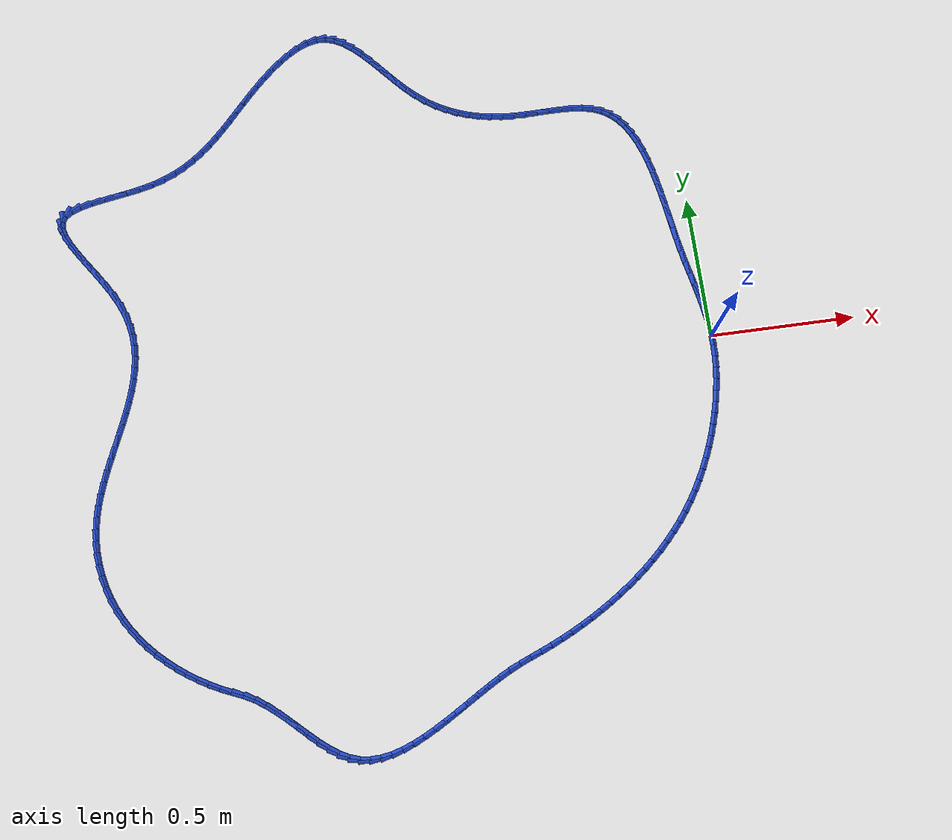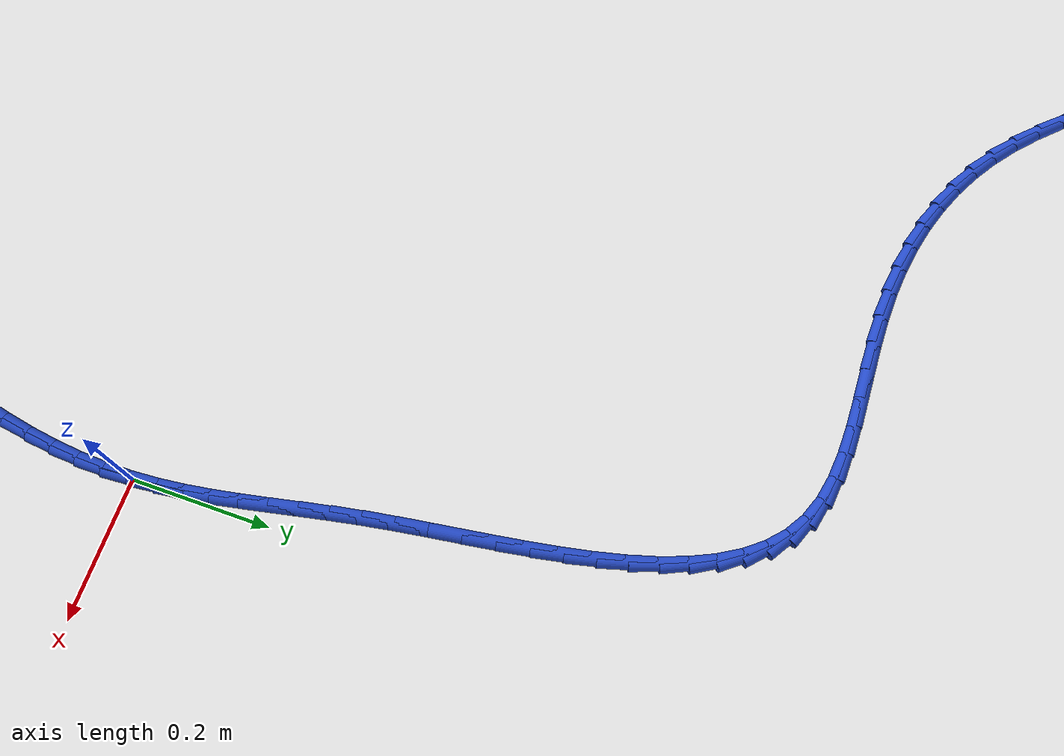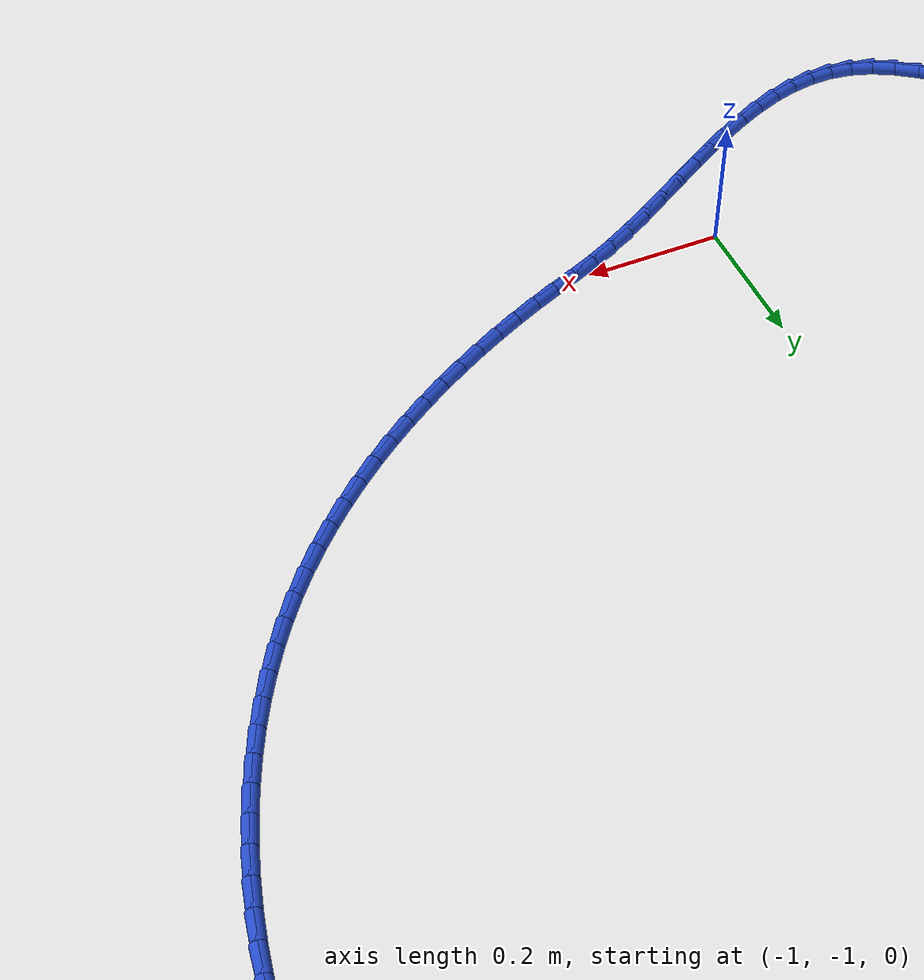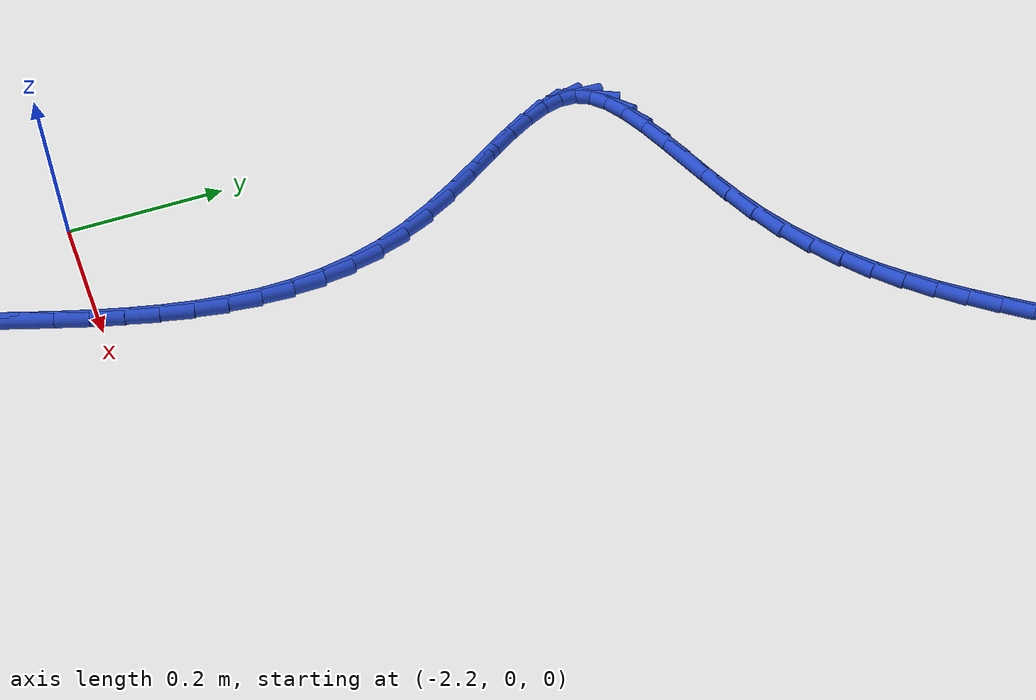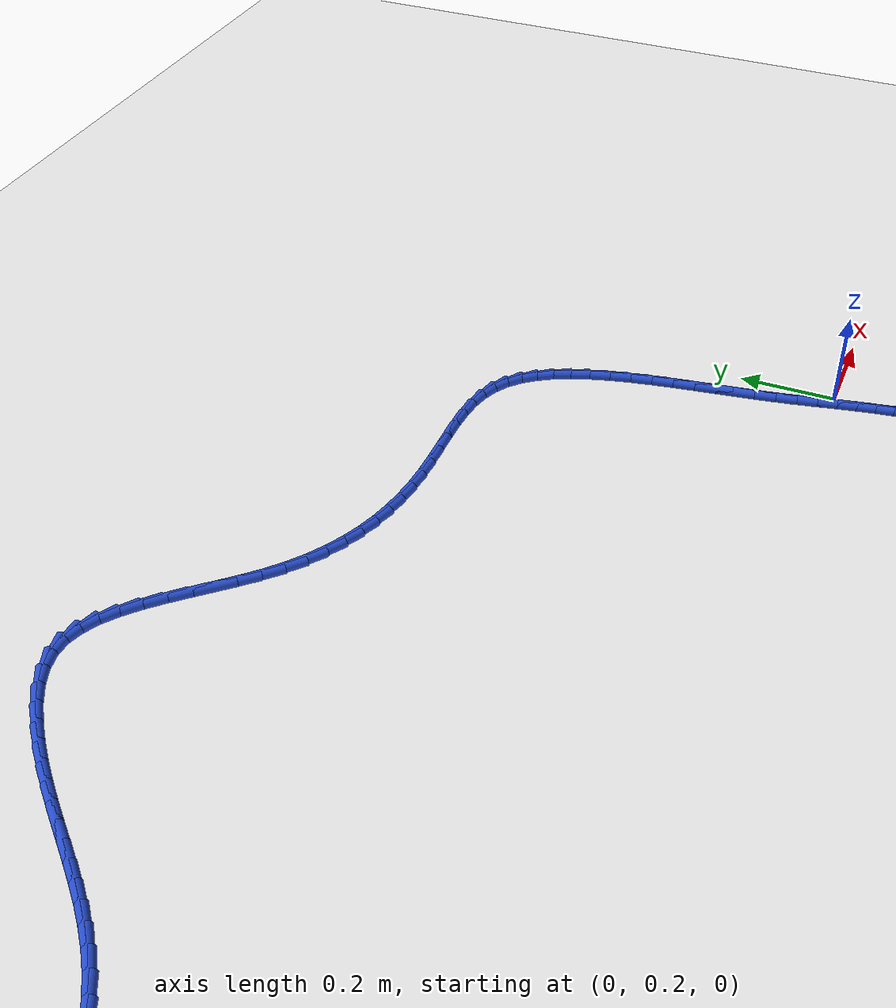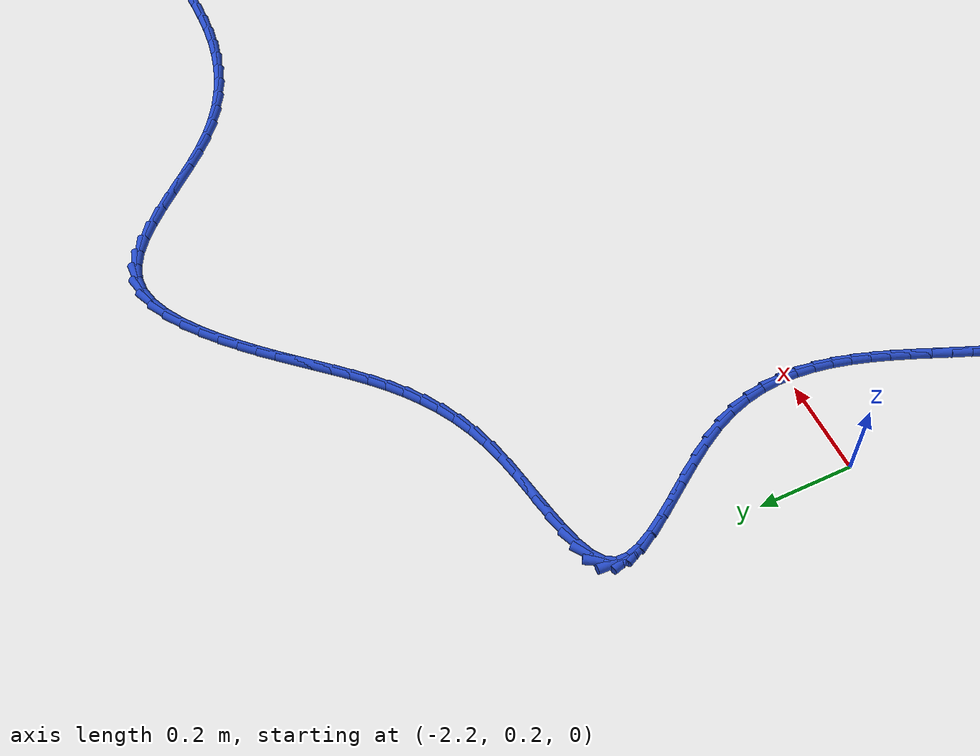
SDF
<sdf version="1.6">
 <world name="default">
  <light name="sun" type="directional">
   <pose>0 0 10 0 -0 0</pose>
   <diffuse>0.8 0.8 0.8 1</diffuse>
   <specular>0.2 0.2 0.2 1</specular>
   <attenuation>
    <range>1000</range>
    <constant>0.9</constant>
    <linear>0.01</linear>
    <quadratic>0.001</quadratic>
   </attenuation>
   <direction>-0.5 0.1 -0.9</direction>
  </light>
  <model name="ground_plane">
   <static>1</static>
   <link name="link">
    <collision name="collision">
     <geometry><plane><normal>0 0 1</normal><size>100 100</size></plane></geometry>
     <surface><friction><ode><mu>100</mu><mu2>50</mu2></ode></friction></surface>
    </collision>
    <visual name="visual">
     <cast_shadows>0</cast_shadows>
     <geometry><plane><normal>0 0 1</normal><size>100 100</size></plane></geometry>
     <material>
      <script><uri>file://media/materials/scripts/gazebo.material</uri><name>Gazebo/WhiteGlow</name></script>
     </material>
    </visual>
   </link>
  </model>
  <gravity>0 0 -9.8</gravity>
  <magnetic_field>6e-06 2.3e-05 -4.2e-05</magnetic_field>
  <atmosphere type="adiabatic"/>
  <physics name="default_physics" default="0" type="ode">
   <max_step_size>0.001</max_step_size>
   <real_time_factor>1</real_time_factor>
   <real_time_update_rate>1000</real_time_update_rate>
  </physics>
  <scene><ambient>0.4 0.4 0.4 1</ambient><background>0.7 0.7 0.7 1</background><shadows>1</shadows></scene>
  <spherical_coordinates>
   <surface_model>EARTH_WGS84</surface_model>
   <latitude_deg>0</latitude_deg>
   <longitude_deg>0</longitude_deg>
   <elevation>0</elevation>
   <heading_deg>0</heading_deg>
  </spherical_coordinates>
  <model name="line">
   <link name="link_0">
    <pose>-3.642919299551295e-17 5.551115123125783e-17 0.01 0 1.57 -1.5058916821787278</pose>
    <collision name="collision">
     <geometry><cylinder><radius>0.01</radius><length>0.08</length></cylinder></geometry>
    </collision>
    <visual name="visual">
     <material>
      <script><name>Gazebo/Blue</name><uri>file://media/materials/scripts/gazebo.material</uri></script>
     </material>
     <geometry><cylinder><radius>0.01</radius><length>0.08</length></cylinder></geometry>
    </visual>
   </link>
   <link name="link_1">
    <pose>-0.0024704983119583856 0.03801004177049731 0.01 0 1.57 -1.4568781691883872</pose>
    <collision name="collision">
     <geometry><cylinder><radius>0.01</radius><length>0.08</length></cylinder></geometry>
    </collision>
    <visual name="visual">
     <material>
      <script><name>Gazebo/Blue</name><uri>file://media/materials/scripts/gazebo.material</uri></script>
     </material>
     <geometry><cylinder><radius>0.01</radius><length>0.08</length></cylinder></geometry>
    </visual>
   </link>
   <link name="link_2">
    <pose>-0.006784700317970747 0.0757171433615318 0.01 0 1.57 -1.4178943917646176</pose>
    <collision name="collision">
     <geometry><cylinder><radius>0.01</radius><length>0.08</length></cylinder></geometry>
    </collision>
    <visual name="visual">
     <material>
      <script><name>Gazebo/Blue</name><uri>file://media/materials/scripts/gazebo.material</uri></script>
     </material>
     <geometry><cylinder><radius>0.01</radius><length>0.08</length></cylinder></geometry>
    </visual>
   </link>
   <link name="link_3">
    <pose>-0.012589108862499433 0.11338248831321925 0.01 0 1.57 -1.3895895218170407</pose>
    <collision name="collision">
     <geometry><cylinder><radius>0.01</radius><length>0.08</length></cylinder></geometry>
    </collision>
    <visual name="visual">
     <material>
      <script><name>Gazebo/Blue</name><uri>file://media/materials/scripts/gazebo.material</uri></script>
     </material>
     <geometry><cylinder><radius>0.01</radius><length>0.08</length></cylinder></geometry>
    </visual>
   </link>
   <link name="link_4">
    <pose>-0.019530226790006763 0.15126726016567543 0.01 0 1.57 -1.372116543712745</pose>
    <collision name="collision">
     <geometry><cylinder><radius>0.01</radius><length>0.08</length></cylinder></geometry>
    </collision>
    <visual name="visual">
     <material>
      <script><name>Gazebo/Blue</name><uri>file://media/materials/scripts/gazebo.material</uri></script>
     </material>
     <geometry><cylinder><radius>0.01</radius><length>0.08</length></cylinder></geometry>
    </visual>
   </link>
   <link name="link_5">
    <pose>-0.027254556944955058 0.18963264245901604 0.01 0 1.57 -1.3652363332114648</pose>
    <collision name="collision">
     <geometry><cylinder><radius>0.01</radius><length>0.08</length></cylinder></geometry>
    </collision>
    <visual name="visual">
     <material>
      <script><name>Gazebo/Blue</name><uri>file://media/materials/scripts/gazebo.material</uri></script>
     </material>
     <geometry><cylinder><radius>0.01</radius><length>0.08</length></cylinder></geometry>
    </visual>
   </link>
   <link name="link_6">
    <pose>-0.03540860217180663 0.2287398187333568 0.01 0 1.57 -1.3684139475995292</pose>
    <collision name="collision">
     <geometry><cylinder><radius>0.01</radius><length>0.08</length></cylinder></geometry>
    </collision>
    <visual name="visual">
     <material>
      <script><name>Gazebo/Blue</name><uri>file://media/materials/scripts/gazebo.material</uri></script>
     </material>
     <geometry><cylinder><radius>0.01</radius><length>0.08</length></cylinder></geometry>
    </visual>
   </link>
   <link name="link_7">
    <pose>-0.0436388653150238 0.2688499725288135 0.01 0 1.57 -1.380892299765392</pose>
    <collision name="collision">
     <geometry><cylinder><radius>0.01</radius><length>0.08</length></cylinder></geometry>
    </collision>
    <visual name="visual">
     <material>
      <script><name>Gazebo/Blue</name><uri>file://media/materials/scripts/gazebo.material</uri></script>
     </material>
     <geometry><cylinder><radius>0.01</radius><length>0.08</length></cylinder></geometry>
    </visual>
   </link>
   <link name="link_8">
    <pose>-0.05159184921906886 0.3102242873855017 0.01 0 1.57 -1.4008927814023446</pose>
    <collision name="collision">
     <geometry><cylinder><radius>0.01</radius><length>0.08</length></cylinder></geometry>
    </collision>
    <visual name="visual">
     <material>
      <script><name>Gazebo/Blue</name><uri>file://media/materials/scripts/gazebo.material</uri></script>
     </material>
     <geometry><cylinder><radius>0.01</radius><length>0.08</length></cylinder></geometry>
    </visual>
   </link>
   <link name="link_9">
    <pose>-0.05894560707069789 0.35308896360972175 0.01 0 1.57 -1.417779490976197</pose>
    <collision name="collision">
     <geometry><cylinder><radius>0.01</radius><length>0.08</length></cylinder></geometry>
    </collision>
    <visual name="visual">
     <material>
      <script><name>Gazebo/Blue</name><uri>file://media/materials/scripts/gazebo.material</uri></script>
     </material>
     <geometry><cylinder><radius>0.01</radius><length>0.08</length></cylinder></geometry>
    </visual>
   </link>
   <link name="link_10">
    <pose>-0.06575636336411009 0.3972508825936538 0.01 0 1.57 -1.4257110879423016</pose>
    <collision name="collision">
     <geometry><cylinder><radius>0.01</radius><length>0.08</length></cylinder></geometry>
    </collision>
    <visual name="visual">
     <material>
      <script><name>Gazebo/Blue</name><uri>file://media/materials/scripts/gazebo.material</uri></script>
     </material>
     <geometry><cylinder><radius>0.01</radius><length>0.08</length></cylinder></geometry>
    </visual>
   </link>
   <link name="link_11">
    <pose>-0.07232984795040258 0.44224027249518477 0.01 0 1.57 -1.4252506819312438</pose>
    <collision name="collision">
     <geometry><cylinder><radius>0.01</radius><length>0.08</length></cylinder></geometry>
    </collision>
    <visual name="visual">
     <material>
      <script><name>Gazebo/Blue</name><uri>file://media/materials/scripts/gazebo.material</uri></script>
     </material>
     <geometry><cylinder><radius>0.01</radius><length>0.08</length></cylinder></geometry>
    </visual>
   </link>
   <link name="link_12">
    <pose>-0.07897620447169766 0.4875824674307357 0.01 0 1.57 -1.4165833960718521</pose>
    <collision name="collision">
     <geometry><cylinder><radius>0.01</radius><length>0.08</length></cylinder></geometry>
    </collision>
    <visual name="visual">
     <material>
      <script><name>Gazebo/Blue</name><uri>file://media/materials/scripts/gazebo.material</uri></script>
     </material>
     <geometry><cylinder><radius>0.01</radius><length>0.08</length></cylinder></geometry>
    </visual>
   </link>
   <link name="link_13">
    <pose>-0.08600557657011755 0.532802801516727 0.01 0 1.57 -1.3994350408714065</pose>
    <collision name="collision">
     <geometry><cylinder><radius>0.01</radius><length>0.08</length></cylinder></geometry>
    </collision>
    <visual name="visual">
     <material>
      <script><name>Gazebo/Blue</name><uri>file://media/materials/scripts/gazebo.material</uri></script>
     </material>
     <geometry><cylinder><radius>0.01</radius><length>0.08</length></cylinder></geometry>
    </visual>
   </link>
   <link name="link_14">
    <pose>-0.09372810788778446 0.5774266088695794 0.01 0 1.57 -1.3730627541175686</pose>
    <collision name="collision">
     <geometry><cylinder><radius>0.01</radius><length>0.08</length></cylinder></geometry>
    </collision>
    <visual name="visual">
     <material>
      <script><name>Gazebo/Blue</name><uri>file://media/materials/scripts/gazebo.material</uri></script>
     </material>
     <geometry><cylinder><radius>0.01</radius><length>0.08</length></cylinder></geometry>
    </visual>
   </link>
   <link name="link_15">
    <pose>-0.10245394206682074 0.6209792236057141 0.01 0 1.57 -1.336204620259618</pose>
    <collision name="collision">
     <geometry><cylinder><radius>0.01</radius><length>0.08</length></cylinder></geometry>
    </collision>
    <visual name="visual">
     <material>
      <script><name>Gazebo/Blue</name><uri>file://media/materials/scripts/gazebo.material</uri></script>
     </material>
     <geometry><cylinder><radius>0.01</radius><length>0.08</length></cylinder></geometry>
    </visual>
   </link>
   <link name="link_16">
    <pose>-0.11249322274934863 0.662985979841552 0.01 0 1.57 -1.2869971500145743</pose>
    <collision name="collision">
     <geometry><cylinder><radius>0.01</radius><length>0.08</length></cylinder></geometry>
    </collision>
    <visual name="visual">
     <material>
      <script><name>Gazebo/Blue</name><uri>file://media/materials/scripts/gazebo.material</uri></script>
     </material>
     <geometry><cylinder><radius>0.01</radius><length>0.08</length></cylinder></geometry>
    </visual>
   </link>
   <link name="link_17">
    <pose>-0.12415609357749036 0.7029722116935134 0.01 0 1.57 -1.2228854900770947</pose>
    <collision name="collision">
     <geometry><cylinder><radius>0.01</radius><length>0.08</length></cylinder></geometry>
    </collision>
    <visual name="visual">
     <material>
      <script><name>Gazebo/Blue</name><uri>file://media/materials/scripts/gazebo.material</uri></script>
     </material>
     <geometry><cylinder><radius>0.01</radius><length>0.08</length></cylinder></geometry>
    </visual>
   </link>
   <link name="link_18">
    <pose>-0.13775269819336816 0.7404632532780194 0.01 0 1.57 -1.1405967226817182</pose>
    <collision name="collision">
     <geometry><cylinder><radius>0.01</radius><length>0.08</length></cylinder></geometry>
    </collision>
    <visual name="visual">
     <material>
      <script><name>Gazebo/Blue</name><uri>file://media/materials/scripts/gazebo.material</uri></script>
     </material>
     <geometry><cylinder><radius>0.01</radius><length>0.08</length></cylinder></geometry>
    </visual>
   </link>
   <link name="link_19">
    <pose>-0.1535931802391043 0.7749844387114908 0.01 0 1.57 -1.0363486107870967</pose>
    <collision name="collision">
     <geometry><cylinder><radius>0.01</radius><length>0.08</length></cylinder></geometry>
    </collision>
    <visual name="visual">
     <material>
      <script><name>Gazebo/Blue</name><uri>file://media/materials/scripts/gazebo.material</uri></script>
     </material>
     <geometry><cylinder><radius>0.01</radius><length>0.08</length></cylinder></geometry>
    </visual>
   </link>
   <link name="link_20">
    <pose>-0.17198768335682113 0.8060611021103483 0.01 0 1.57 -0.9066361919721067</pose>
    <collision name="collision">
     <geometry><cylinder><radius>0.01</radius><length>0.08</length></cylinder></geometry>
    </collision>
    <visual name="visual">
     <material>
      <script><name>Gazebo/Blue</name><uri>file://media/materials/scripts/gazebo.material</uri></script>
     </material>
     <geometry><cylinder><radius>0.01</radius><length>0.08</length></cylinder></geometry>
    </visual>
   </link>
   <link name="link_21">
    <pose>-0.19324635118864075 0.8332185775910127 0.01 0 1.57 -0.7500426726153248</pose>
    <collision name="collision">
     <geometry><cylinder><radius>0.01</radius><length>0.08</length></cylinder></geometry>
    </collision>
    <visual name="visual">
     <material>
      <script><name>Gazebo/Blue</name><uri>file://media/materials/scripts/gazebo.material</uri></script>
     </material>
     <geometry><cylinder><radius>0.01</radius><length>0.08</length></cylinder></geometry>
    </visual>
   </link>
   <link name="link_22">
    <pose>-0.2176793273766857 0.8559821992699053 0.01 0 1.57 -0.570023065147748</pose>
    <collision name="collision">
     <geometry><cylinder><radius>0.01</radius><length>0.08</length></cylinder></geometry>
    </collision>
    <visual name="visual">
     <material>
      <script><name>Gazebo/Blue</name><uri>file://media/materials/scripts/gazebo.material</uri></script>
     </material>
     <geometry><cylinder><radius>0.01</radius><length>0.08</length></cylinder></geometry>
    </visual>
   </link>
   <link name="link_23">
    <pose>-0.2455967555630778 0.8738773012634458 0.01 0 1.57 -0.3810829290091312</pose>
    <collision name="collision">
     <geometry><cylinder><radius>0.01</radius><length>0.08</length></cylinder></geometry>
    </collision>
    <visual name="visual">
     <material>
      <script><name>Gazebo/Blue</name><uri>file://media/materials/scripts/gazebo.material</uri></script>
     </material>
     <geometry><cylinder><radius>0.01</radius><length>0.08</length></cylinder></geometry>
    </visual>
   </link>
   <link name="link_24">
    <pose>-0.27723013281030456 0.8865518134539518 0.01 0 1.57 -0.22504649909694271</pose>
    <collision name="collision">
     <geometry><cylinder><radius>0.01</radius><length>0.08</length></cylinder></geometry>
    </collision>
    <visual name="visual">
     <material>
      <script><name>Gazebo/Blue</name><uri>file://media/materials/scripts/gazebo.material</uri></script>
     </material>
     <geometry><cylinder><radius>0.01</radius><length>0.08</length></cylinder></geometry>
    </visual>
   </link>
   <link name="link_25">
    <pose>-0.31222728002615074 0.8945635110794126 0.01 0 1.57 -0.11384668438913959</pose>
    <collision name="collision">
     <geometry><cylinder><radius>0.01</radius><length>0.08</length></cylinder></geometry>
    </collision>
    <visual name="visual">
     <material>
      <script><name>Gazebo/Blue</name><uri>file://media/materials/scripts/gazebo.material</uri></script>
     </material>
     <geometry><cylinder><radius>0.01</radius><length>0.08</length></cylinder></geometry>
    </visual>
   </link>
   <link name="link_26">
    <pose>-0.3499734593183888 0.8988794509680602 0.01 0 1.57 -0.039829299469846584</pose>
    <collision name="collision">
     <geometry><cylinder><radius>0.01</radius><length>0.08</length></cylinder></geometry>
    </collision>
    <visual name="visual">
     <material>
      <script><name>Gazebo/Blue</name><uri>file://media/materials/scripts/gazebo.material</uri></script>
     </material>
     <geometry><cylinder><radius>0.01</radius><length>0.08</length></cylinder></geometry>
    </visual>
   </link>
   <link name="link_27">
    <pose>-0.3898526737400347 0.900468652586334 0.01 0 1.57 0.004070809413849645</pose>
    <collision name="collision">
     <geometry><cylinder><radius>0.01</radius><length>0.08</length></cylinder></geometry>
    </collision>
    <visual name="visual">
     <material>
      <script><name>Gazebo/Blue</name><uri>file://media/materials/scripts/gazebo.material</uri></script>
     </material>
     <geometry><cylinder><radius>0.01</radius><length>0.08</length></cylinder></geometry>
    </visual>
   </link>
   <link name="link_28">
    <pose>-0.4312489263441052 0.900300135400674 0.01 0 1.57 0.02262681780327256</pose>
    <collision name="collision">
     <geometry><cylinder><radius>0.01</radius><length>0.08</length></cylinder></geometry>
    </collision>
    <visual name="visual">
     <material>
      <script><name>Gazebo/Blue</name><uri>file://media/materials/scripts/gazebo.material</uri></script>
     </material>
     <geometry><cylinder><radius>0.01</radius><length>0.08</length></cylinder></geometry>
    </visual>
   </link>
   <link name="link_29">
    <pose>-0.473546220183617 0.8993429188775187 0.01 0 1.57 0.018242544801845822</pose>
    <collision name="collision">
     <geometry><cylinder><radius>0.01</radius><length>0.08</length></cylinder></geometry>
    </collision>
    <visual name="visual">
     <material>
      <script><name>Gazebo/Blue</name><uri>file://media/materials/scripts/gazebo.material</uri></script>
     </material>
     <geometry><cylinder><radius>0.01</radius><length>0.08</length></cylinder></geometry>
    </visual>
   </link>
   <link name="link_30">
    <pose>-0.5161285583115862 0.8985660224833086 0.01 0 1.57 -0.008814706330348086</pose>
    <collision name="collision">
     <geometry><cylinder><radius>0.01</radius><length>0.08</length></cylinder></geometry>
    </collision>
    <visual name="visual">
     <material>
      <script><name>Gazebo/Blue</name><uri>file://media/materials/scripts/gazebo.material</uri></script>
     </material>
     <geometry><cylinder><radius>0.01</radius><length>0.08</length></cylinder></geometry>
    </visual>
   </link>
   <link name="link_31">
    <pose>-0.55837994378103 0.8989384656844828 0.01 0 1.57 -0.057781774671474884</pose>
    <collision name="collision">
     <geometry><cylinder><radius>0.01</radius><length>0.08</length></cylinder></geometry>
    </collision>
    <visual name="visual">
     <material>
      <script><name>Gazebo/Blue</name><uri>file://media/materials/scripts/gazebo.material</uri></script>
     </material>
     <geometry><cylinder><radius>0.01</radius><length>0.08</length></cylinder></geometry>
    </visual>
   </link>
   <link name="link_32">
    <pose>-0.5997562188710199 0.9013319245886888 0.01 0 1.57 -0.11715414385520997</pose>
    <collision name="collision">
     <geometry><cylinder><radius>0.01</radius><length>0.08</length></cylinder></geometry>
    </collision>
    <visual name="visual">
     <material>
      <script><name>Gazebo/Blue</name><uri>file://media/materials/scripts/gazebo.material</uri></script>
     </material>
     <geometry><cylinder><radius>0.01</radius><length>0.08</length></cylinder></geometry>
    </visual>
   </link>
   <link name="link_33">
    <pose>-0.6401094255657769 0.9060812180437094 0.01 0 1.57 -0.18249003665453106</pose>
    <collision name="collision">
     <geometry><cylinder><radius>0.01</radius><length>0.08</length></cylinder></geometry>
    </collision>
    <visual name="visual">
     <material>
      <script><name>Gazebo/Blue</name><uri>file://media/materials/scripts/gazebo.material</uri></script>
     </material>
     <geometry><cylinder><radius>0.01</radius><length>0.08</length></cylinder></geometry>
    </visual>
   </link>
   <link name="link_34">
    <pose>-0.6794274513714881 0.913337091931746 0.01 0 1.57 -0.25345281989264795</pose>
    <collision name="collision">
     <geometry><cylinder><radius>0.01</radius><length>0.08</length></cylinder></geometry>
    </collision>
    <visual name="visual">
     <material>
      <script><name>Gazebo/Blue</name><uri>file://media/materials/scripts/gazebo.material</uri></script>
     </material>
     <geometry><cylinder><radius>0.01</radius><length>0.08</length></cylinder></geometry>
    </visual>
   </link>
   <link name="link_35">
    <pose>-0.7176983049540212 0.9232501279615992 0.01 0 1.57 -0.32939499652450926</pose>
    <collision name="collision">
     <geometry><cylinder><radius>0.01</radius><length>0.08</length></cylinder></geometry>
    </collision>
    <visual name="visual">
     <material>
      <script><name>Gazebo/Blue</name><uri>file://media/materials/scripts/gazebo.material</uri></script>
     </material>
     <geometry><cylinder><radius>0.01</radius><length>0.08</length></cylinder></geometry>
    </visual>
   </link>
   <link name="link_36">
    <pose>-0.7549099949792433 0.935970907842068 0.01 0 1.57 -0.4093318876356937</pose>
    <collision name="collision">
     <geometry><cylinder><radius>0.01</radius><length>0.08</length></cylinder></geometry>
    </collision>
    <visual name="visual">
     <material>
      <script><name>Gazebo/Blue</name><uri>file://media/materials/scripts/gazebo.material</uri></script>
     </material>
     <geometry><cylinder><radius>0.01</radius><length>0.08</length></cylinder></geometry>
    </visual>
   </link>
   <link name="link_37">
    <pose>-0.7910505301130214 0.9516500132819524 0.01 0 1.57 -0.49197026340341876</pose>
    <collision name="collision">
     <geometry><cylinder><radius>0.01</radius><length>0.08</length></cylinder></geometry>
    </collision>
    <visual name="visual">
     <material>
      <script><name>Gazebo/Blue</name><uri>file://media/materials/scripts/gazebo.material</uri></script>
     </material>
     <geometry><cylinder><radius>0.01</radius><length>0.08</length></cylinder></geometry>
    </visual>
   </link>
   <link name="link_38">
    <pose>-0.826107919021223 0.9704380259900524 0.01 0 1.57 -0.575796221264351</pose>
    <collision name="collision">
     <geometry><cylinder><radius>0.01</radius><length>0.08</length></cylinder></geometry>
    </collision>
    <visual name="visual">
     <material>
      <script><name>Gazebo/Blue</name><uri>file://media/materials/scripts/gazebo.material</uri></script>
     </material>
     <geometry><cylinder><radius>0.01</radius><length>0.08</length></cylinder></geometry>
    </visual>
   </link>
   <link name="link_39">
    <pose>-0.8600701703697154 0.9924855276751672 0.01 0 1.57 -0.659212178121632</pose>
    <collision name="collision">
     <geometry><cylinder><radius>0.01</radius><length>0.08</length></cylinder></geometry>
    </collision>
    <visual name="visual">
     <material>
      <script><name>Gazebo/Blue</name><uri>file://media/materials/scripts/gazebo.material</uri></script>
     </material>
     <geometry><cylinder><radius>0.01</radius><length>0.08</length></cylinder></geometry>
    </visual>
   </link>
   <link name="link_40">
    <pose>-0.892925292824366 1.017943100046097 0.01 0 1.57 -0.739719881212941</pose>
    <collision name="collision">
     <geometry><cylinder><radius>0.01</radius><length>0.08</length></cylinder></geometry>
    </collision>
    <visual name="visual">
     <material>
      <script><name>Gazebo/Blue</name><uri>file://media/materials/scripts/gazebo.material</uri></script>
     </material>
     <geometry><cylinder><radius>0.01</radius><length>0.08</length></cylinder></geometry>
    </visual>
   </link>
   <link name="link_41">
    <pose>-0.9246703222853487 1.0469128521050097 0.01 0 1.57 -0.802309994501067</pose>
    <collision name="collision">
     <geometry><cylinder><radius>0.01</radius><length>0.08</length></cylinder></geometry>
    </collision>
    <visual name="visual">
     <material>
      <script><name>Gazebo/Blue</name><uri>file://media/materials/scripts/gazebo.material</uri></script>
     </material>
     <geometry><cylinder><radius>0.01</radius><length>0.08</length></cylinder></geometry>
    </visual>
   </link>
   <link name="link_42">
    <pose>-0.9554425280739394 1.0787438943996 0.01 0 1.57 -0.8388945553541998</pose>
    <collision name="collision">
     <geometry><cylinder><radius>0.01</radius><length>0.08</length></cylinder></geometry>
    </collision>
    <visual name="visual">
     <material>
      <script><name>Gazebo/Blue</name><uri>file://media/materials/scripts/gazebo.material</uri></script>
     </material>
     <geometry><cylinder><radius>0.01</radius><length>0.08</length></cylinder></geometry>
    </visual>
   </link>
   <link name="link_43">
    <pose>-0.9854898325491184 1.1121911740768702 0.01 0 1.57 -0.8520282630070609</pose>
    <collision name="collision">
     <geometry><cylinder><radius>0.01</radius><length>0.08</length></cylinder></geometry>
    </collision>
    <visual name="visual">
     <material>
      <script><name>Gazebo/Blue</name><uri>file://media/materials/scripts/gazebo.material</uri></script>
     </material>
     <geometry><cylinder><radius>0.01</radius><length>0.08</length></cylinder></geometry>
    </visual>
   </link>
   <link name="link_44">
    <pose>-1.0150631649441597 1.1459934925485267 0.01 0 1.57 -0.8423016690394987</pose>
    <collision name="collision">
     <geometry><cylinder><radius>0.01</radius><length>0.08</length></cylinder></geometry>
    </collision>
    <visual name="visual">
     <material>
      <script><name>Gazebo/Blue</name><uri>file://media/materials/scripts/gazebo.material</uri></script>
     </material>
     <geometry><cylinder><radius>0.01</radius><length>0.08</length></cylinder></geometry>
    </visual>
   </link>
   <link name="link_45">
    <pose>-1.0444134544923374 1.1788896512262756 0.01 0 1.57 -0.8078647254685356</pose>
    <collision name="collision">
     <geometry><cylinder><radius>0.01</radius><length>0.08</length></cylinder></geometry>
    </collision>
    <visual name="visual">
     <material>
      <script><name>Gazebo/Blue</name><uri>file://media/materials/scripts/gazebo.material</uri></script>
     </material>
     <geometry><cylinder><radius>0.01</radius><length>0.08</length></cylinder></geometry>
    </visual>
   </link>
   <link name="link_46">
    <pose>-1.0737916304269262 1.2096184515218242 0.01 0 1.57 -0.7440442490150625</pose>
    <collision name="collision">
     <geometry><cylinder><radius>0.01</radius><length>0.08</length></cylinder></geometry>
    </collision>
    <visual name="visual">
     <material>
      <script><name>Gazebo/Blue</name><uri>file://media/materials/scripts/gazebo.material</uri></script>
     </material>
     <geometry><cylinder><radius>0.01</radius><length>0.08</length></cylinder></geometry>
    </visual>
   </link>
   <link name="link_47">
    <pose>-1.1034486219811999 1.236918694846878 0.01 0 1.57 -0.642874005500789</pose>
    <collision name="collision">
     <geometry><cylinder><radius>0.01</radius><length>0.08</length></cylinder></geometry>
    </collision>
    <visual name="visual">
     <material>
      <script><name>Gazebo/Blue</name><uri>file://media/materials/scripts/gazebo.material</uri></script>
     </material>
     <geometry><cylinder><radius>0.01</radius><length>0.08</length></cylinder></geometry>
    </visual>
   </link>
   <link name="link_48">
    <pose>-1.1336353583884327 1.259529182613144 0.01 0 1.57 -0.49356013040534336</pose>
    <collision name="collision">
     <geometry><cylinder><radius>0.01</radius><length>0.08</length></cylinder></geometry>
    </collision>
    <visual name="visual">
     <material>
      <script><name>Gazebo/Blue</name><uri>file://media/materials/scripts/gazebo.material</uri></script>
     </material>
     <geometry><cylinder><radius>0.01</radius><length>0.08</length></cylinder></geometry>
    </visual>
   </link>
   <link name="link_49">
    <pose>-1.1646027688818992 1.2761887162323287 0.01 0 1.57 -0.28708389258035083</pose>
    <collision name="collision">
     <geometry><cylinder><radius>0.01</radius><length>0.08</length></cylinder></geometry>
    </collision>
    <visual name="visual">
     <material>
      <script><name>Gazebo/Blue</name><uri>file://media/materials/scripts/gazebo.material</uri></script>
     </material>
     <geometry><cylinder><radius>0.01</radius><length>0.08</length></cylinder></geometry>
    </visual>
   </link>
   <link name="link_50">
    <pose>-1.196601782694874 1.2856360971161382 0.01 0 1.57 -0.02963732144660762</pose>
    <collision name="collision">
     <geometry><cylinder><radius>0.01</radius><length>0.08</length></cylinder></geometry>
    </collision>
    <visual name="visual">
     <material>
      <script><name>Gazebo/Blue</name><uri>file://media/materials/scripts/gazebo.material</uri></script>
     </material>
     <geometry><cylinder><radius>0.01</radius><length>0.08</length></cylinder></geometry>
    </visual>
   </link>
   <link name="link_51">
    <pose>-1.2298794530847537 1.2866226469996043 0.01 0 1.57 0.22104520568271016</pose>
    <collision name="collision">
     <geometry><cylinder><radius>0.01</radius><length>0.08</length></cylinder></geometry>
    </collision>
    <visual name="visual">
     <material>
      <script><name>Gazebo/Blue</name><uri>file://media/materials/scripts/gazebo.material</uri></script>
     </material>
     <geometry><cylinder><radius>0.01</radius><length>0.08</length></cylinder></geometry>
    </visual>
   </link>
   <link name="link_52">
    <pose>-1.2643827046136848 1.278869174637991 0.01 0 1.57 0.4062692847931407</pose>
    <collision name="collision">
     <geometry><cylinder><radius>0.01</radius><length>0.08</length></cylinder></geometry>
    </collision>
    <visual name="visual">
     <material>
      <script><name>Gazebo/Blue</name><uri>file://media/materials/scripts/gazebo.material</uri></script>
     </material>
     <geometry><cylinder><radius>0.01</radius><length>0.08</length></cylinder></geometry>
    </visual>
   </link>
   <link name="link_53">
    <pose>-1.2995495854542731 1.2637402804744995 0.01 0 1.57 0.5372585897245692</pose>
    <collision name="collision">
     <geometry><cylinder><radius>0.01</radius><length>0.08</length></cylinder></geometry>
    </collision>
    <visual name="visual">
     <material>
      <script><name>Gazebo/Blue</name><uri>file://media/materials/scripts/gazebo.material</uri></script>
     </material>
     <geometry><cylinder><radius>0.01</radius><length>0.08</length></cylinder></geometry>
    </visual>
   </link>
   <link name="link_54">
    <pose>-1.334768834057124 1.2427598470743213 0.01 0 1.57 0.6306912610560182</pose>
    <collision name="collision">
     <geometry><cylinder><radius>0.01</radius><length>0.08</length></cylinder></geometry>
    </collision>
    <visual name="visual">
     <material>
      <script><name>Gazebo/Blue</name><uri>file://media/materials/scripts/gazebo.material</uri></script>
     </material>
     <geometry><cylinder><radius>0.01</radius><length>0.08</length></cylinder></geometry>
    </visual>
   </link>
   <link name="link_55">
    <pose>-1.3694291888728427 1.2174517570026493 0.01 0 1.57 0.6983112795040243</pose>
    <collision name="collision">
     <geometry><cylinder><radius>0.01</radius><length>0.08</length></cylinder></geometry>
    </collision>
    <visual name="visual">
     <material>
      <script><name>Gazebo/Blue</name><uri>file://media/materials/scripts/gazebo.material</uri></script>
     </material>
     <geometry><cylinder><radius>0.01</radius><length>0.08</length></cylinder></geometry>
    </visual>
   </link>
   <link name="link_56">
    <pose>-1.4029193883520341 1.1893398928246766 0.01 0 1.57 0.7476247107921191</pose>
    <collision name="collision">
     <geometry><cylinder><radius>0.01</radius><length>0.08</length></cylinder></geometry>
    </collision>
    <visual name="visual">
     <material>
      <script><name>Gazebo/Blue</name><uri>file://media/materials/scripts/gazebo.material</uri></script>
     </material>
     <geometry><cylinder><radius>0.01</radius><length>0.08</length></cylinder></geometry>
    </visual>
   </link>
   <link name="link_57">
    <pose>-1.434648986679044 1.159921176643715 0.01 0 1.57 0.7852584218598492</pose>
    <collision name="collision">
     <geometry><cylinder><radius>0.01</radius><length>0.08</length></cylinder></geometry>
    </collision>
    <visual name="visual">
     <material>
      <script><name>Gazebo/Blue</name><uri>file://media/materials/scripts/gazebo.material</uri></script>
     </material>
     <geometry><cylinder><radius>0.01</radius><length>0.08</length></cylinder></geometry>
    </visual>
   </link>
   <link name="link_58">
    <pose>-1.464507088755456 1.130071418235588 0.01 0 1.57 0.8140115126762537</pose>
    <collision name="collision">
     <geometry><cylinder><radius>0.01</radius><length>0.08</length></cylinder></geometry>
    </collision>
    <visual name="visual">
     <material>
      <script><name>Gazebo/Blue</name><uri>file://media/materials/scripts/gazebo.material</uri></script>
     </material>
     <geometry><cylinder><radius>0.01</radius><length>0.08</length></cylinder></geometry>
    </visual>
   </link>
   <link name="link_59">
    <pose>-1.4928627888550439 1.1000447469043513 0.01 0 1.57 0.8331291239726535</pose>
    <collision name="collision">
     <geometry><cylinder><radius>0.01</radius><length>0.08</length></cylinder></geometry>
    </collision>
    <visual name="visual">
     <material>
      <script><name>Gazebo/Blue</name><uri>file://media/materials/scripts/gazebo.material</uri></script>
     </material>
     <geometry><cylinder><radius>0.01</radius><length>0.08</length></cylinder></geometry>
    </visual>
   </link>
   <link name="link_60">
    <pose>-1.5201060847163335 1.0700682178632936 0.01 0 1.57 0.8418736132932424</pose>
    <collision name="collision">
     <geometry><cylinder><radius>0.01</radius><length>0.08</length></cylinder></geometry>
    </collision>
    <visual name="visual">
     <material>
      <script><name>Gazebo/Blue</name><uri>file://media/materials/scripts/gazebo.material</uri></script>
     </material>
     <geometry><cylinder><radius>0.01</radius><length>0.08</length></cylinder></geometry>
    </visual>
   </link>
   <link name="link_61">
    <pose>-1.5466269740778507 1.0403688863257041 0.01 0 1.57 0.8396317648700947</pose>
    <collision name="collision">
     <geometry><cylinder><radius>0.01</radius><length>0.08</length></cylinder></geometry>
    </collision>
    <visual name="visual">
     <material>
      <script><name>Gazebo/Blue</name><uri>file://media/materials/scripts/gazebo.material</uri></script>
     </material>
     <geometry><cylinder><radius>0.01</radius><length>0.08</length></cylinder></geometry>
    </visual>
   </link>
   <link name="link_62">
    <pose>-1.5728154546781208 1.0111738075048717 0.01 0 1.57 0.8259116765790597</pose>
    <collision name="collision">
     <geometry><cylinder><radius>0.01</radius><length>0.08</length></cylinder></geometry>
    </collision>
    <visual name="visual">
     <material>
      <script><name>Gazebo/Blue</name><uri>file://media/materials/scripts/gazebo.material</uri></script>
     </material>
     <geometry><cylinder><radius>0.01</radius><length>0.08</length></cylinder></geometry>
    </visual>
   </link>
   <link name="link_63">
    <pose>-1.5990615242556712 0.9827100366140864 0.01 0 1.57 0.8003742663989084</pose>
    <collision name="collision">
     <geometry><cylinder><radius>0.01</radius><length>0.08</length></cylinder></geometry>
    </collision>
    <visual name="visual">
     <material>
      <script><name>Gazebo/Blue</name><uri>file://media/materials/scripts/gazebo.material</uri></script>
     </material>
     <geometry><cylinder><radius>0.01</radius><length>0.08</length></cylinder></geometry>
    </visual>
   </link>
   <link name="link_64">
    <pose>-1.625755180549027 0.955204628866636 0.01 0 1.57 0.7629094077563804</pose>
    <collision name="collision">
     <geometry><cylinder><radius>0.01</radius><length>0.08</length></cylinder></geometry>
    </collision>
    <visual name="visual">
     <material>
      <script><name>Gazebo/Blue</name><uri>file://media/materials/scripts/gazebo.material</uri></script>
     </material>
     <geometry><cylinder><radius>0.01</radius><length>0.08</length></cylinder></geometry>
    </visual>
   </link>
   <link name="link_65">
    <pose>-1.6532864212967147 0.9288846394758106 0.01 0 1.57 0.7137570551265782</pose>
    <collision name="collision">
     <geometry><cylinder><radius>0.01</radius><length>0.08</length></cylinder></geometry>
    </collision>
    <visual name="visual">
     <material>
      <script><name>Gazebo/Blue</name><uri>file://media/materials/scripts/gazebo.material</uri></script>
     </material>
     <geometry><cylinder><radius>0.01</radius><length>0.08</length></cylinder></geometry>
    </visual>
   </link>
   <link name="link_66">
    <pose>-1.6820452442372589 0.9039771236548988 0.01 0 1.57 0.6536557117875759</pose>
    <collision name="collision">
     <geometry><cylinder><radius>0.01</radius><length>0.08</length></cylinder></geometry>
    </collision>
    <visual name="visual">
     <material>
      <script><name>Gazebo/Blue</name><uri>file://media/materials/scripts/gazebo.material</uri></script>
     </material>
     <geometry><cylinder><radius>0.01</radius><length>0.08</length></cylinder></geometry>
    </visual>
   </link>
   <link name="link_67">
    <pose>-1.7124216471091882 0.8807091366171901 0.01 0 1.57 0.583974523613041</pose>
    <collision name="collision">
     <geometry><cylinder><radius>0.01</radius><length>0.08</length></cylinder></geometry>
    </collision>
    <visual name="visual">
     <material>
      <script><name>Gazebo/Blue</name><uri>file://media/materials/scripts/gazebo.material</uri></script>
     </material>
     <geometry><cylinder><radius>0.01</radius><length>0.08</length></cylinder></geometry>
    </visual>
   </link>
   <link name="link_68">
    <pose>-1.7448056276510266 0.8593077335759732 0.01 0 1.57 0.5067617992801143</pose>
    <collision name="collision">
     <geometry><cylinder><radius>0.01</radius><length>0.08</length></cylinder></geometry>
    </collision>
    <visual name="visual">
     <material>
      <script><name>Gazebo/Blue</name><uri>file://media/materials/scripts/gazebo.material</uri></script>
     </material>
     <geometry><cylinder><radius>0.01</radius><length>0.08</length></cylinder></geometry>
    </visual>
   </link>
   <link name="link_69">
    <pose>-1.7795871836013004 0.8399999697445373 0.01 0 1.57 0.4246445764410981</pose>
    <collision name="collision">
     <geometry><cylinder><radius>0.01</radius><length>0.08</length></cylinder></geometry>
    </collision>
    <visual name="visual">
     <material>
      <script><name>Gazebo/Blue</name><uri>file://media/materials/scripts/gazebo.material</uri></script>
     </material>
     <geometry><cylinder><radius>0.01</radius><length>0.08</length></cylinder></geometry>
    </visual>
   </link>
   <link name="link_70">
    <pose>-1.817156312698536 0.823012900336172 0.01 0 1.57 0.34056067282267916</pose>
    <collision name="collision">
     <geometry><cylinder><radius>0.01</radius><length>0.08</length></cylinder></geometry>
    </collision>
    <visual name="visual">
     <material>
      <script><name>Gazebo/Blue</name><uri>file://media/materials/scripts/gazebo.material</uri></script>
     </material>
     <geometry><cylinder><radius>0.01</radius><length>0.08</length></cylinder></geometry>
    </visual>
   </link>
   <link name="link_71">
    <pose>-1.85790301268126 0.8085735805641662 0.01 0 1.57 0.25893469303975775</pose>
    <collision name="collision">
     <geometry><cylinder><radius>0.01</radius><length>0.08</length></cylinder></geometry>
    </collision>
    <visual name="visual">
     <material>
      <script><name>Gazebo/Blue</name><uri>file://media/materials/scripts/gazebo.material</uri></script>
     </material>
     <geometry><cylinder><radius>0.01</radius><length>0.08</length></cylinder></geometry>
    </visual>
   </link>
   <link name="link_72">
    <pose>-1.9021229250513434 0.796860558507182 0.01 0 1.57 0.19965081665937945</pose>
    <collision name="collision">
     <geometry><cylinder><radius>0.01</radius><length>0.08</length></cylinder></geometry>
    </collision>
    <visual name="visual">
     <material>
      <script><name>Gazebo/Blue</name><uri>file://media/materials/scripts/gazebo.material</uri></script>
     </material>
     <geometry><cylinder><radius>0.01</radius><length>0.08</length></cylinder></geometry>
    </visual>
   </link>
   <link name="link_73">
    <pose>-1.9488524168520376 0.7874050080176257 0.01 0 1.57 0.16989951040424894</pose>
    <collision name="collision">
     <geometry><cylinder><radius>0.01</radius><length>0.08</length></cylinder></geometry>
    </collision>
    <visual name="visual">
     <material>
      <script><name>Gazebo/Blue</name><uri>file://media/materials/scripts/gazebo.material</uri></script>
     </material>
     <geometry><cylinder><radius>0.01</radius><length>0.08</length></cylinder></geometry>
    </visual>
   </link>
   <link name="link_74">
    <pose>-1.9962310133566203 0.7792770499638326 0.01 0 1.57 0.16617751286514482</pose>
    <collision name="collision">
     <geometry><cylinder><radius>0.01</radius><length>0.08</length></cylinder></geometry>
    </collision>
    <visual name="visual">
     <material>
      <script><name>Gazebo/Blue</name><uri>file://media/materials/scripts/gazebo.material</uri></script>
     </material>
     <geometry><cylinder><radius>0.01</radius><length>0.08</length></cylinder></geometry>
    </visual>
   </link>
   <link name="link_75">
    <pose>-2.0423789979957303 0.7715369132696901 0.01 0 1.57 0.19033812575177786</pose>
    <collision name="collision">
     <geometry><cylinder><radius>0.01</radius><length>0.08</length></cylinder></geometry>
    </collision>
    <visual name="visual">
     <material>
      <script><name>Gazebo/Blue</name><uri>file://media/materials/scripts/gazebo.material</uri></script>
     </material>
     <geometry><cylinder><radius>0.01</radius><length>0.08</length></cylinder></geometry>
    </visual>
   </link>
   <link name="link_76">
    <pose>-2.085416654200007 0.7632448268590861 0.01 0 1.57 0.2516933184098098</pose>
    <collision name="collision">
     <geometry><cylinder><radius>0.01</radius><length>0.08</length></cylinder></geometry>
    </collision>
    <visual name="visual">
     <material>
      <script><name>Gazebo/Blue</name><uri>file://media/materials/scripts/gazebo.material</uri></script>
     </material>
     <geometry><cylinder><radius>0.01</radius><length>0.08</length></cylinder></geometry>
    </visual>
   </link>
   <link name="link_77">
    <pose>-2.123464265400093 0.7534610196559086 0.01 0 1.57 0.3734124134598107</pose>
    <collision name="collision">
     <geometry><cylinder><radius>0.01</radius><length>0.08</length></cylinder></geometry>
    </collision>
    <visual name="visual">
     <material>
      <script><name>Gazebo/Blue</name><uri>file://media/materials/scripts/gazebo.material</uri></script>
     </material>
     <geometry><cylinder><radius>0.01</radius><length>0.08</length></cylinder></geometry>
    </visual>
   </link>
   <link name="link_78">
    <pose>-2.1546421150266255 0.7412457205840448 0.01 0 1.57 0.60732761095877</pose>
    <collision name="collision">
     <geometry><cylinder><radius>0.01</radius><length>0.08</length></cylinder></geometry>
    </collision>
    <visual name="visual">
     <material>
      <script><name>Gazebo/Blue</name><uri>file://media/materials/scripts/gazebo.material</uri></script>
     </material>
     <geometry><cylinder><radius>0.01</radius><length>0.08</length></cylinder></geometry>
    </visual>
   </link>
   <link name="link_79">
    <pose>-2.1770704865102455 0.7256591585673826 0.01 0 1.57 1.0334572947745657</pose>
    <collision name="collision">
     <geometry><cylinder><radius>0.01</radius><length>0.08</length></cylinder></geometry>
    </collision>
    <visual name="visual">
     <material>
      <script><name>Gazebo/Blue</name><uri>file://media/materials/scripts/gazebo.material</uri></script>
     </material>
     <geometry><cylinder><radius>0.01</radius><length>0.08</length></cylinder></geometry>
    </visual>
   </link>
   <link name="link_80">
    <pose>-2.1889148319844773 0.7057800345244812 0.01 0 1.57 1.5303227682311096</pose>
    <collision name="collision">
     <geometry><cylinder><radius>0.01</radius><length>0.08</length></cylinder></geometry>
    </collision>
    <visual name="visual">
     <material>
      <script><name>Gazebo/Blue</name><uri>file://media/materials/scripts/gazebo.material</uri></script>
     </material>
     <geometry><cylinder><radius>0.01</radius><length>0.08</length></cylinder></geometry>
    </visual>
   </link>
   <link name="link_81">
    <pose>-2.189905080117014 0.6813268508372244 0.01 0 1.57 -1.2906413061240363</pose>
    <collision name="collision">
     <geometry><cylinder><radius>0.01</radius><length>0.08</length></cylinder></geometry>
    </collision>
    <visual name="visual">
     <material>
      <script><name>Gazebo/Blue</name><uri>file://media/materials/scripts/gazebo.material</uri></script>
     </material>
     <geometry><cylinder><radius>0.01</radius><length>0.08</length></cylinder></geometry>
    </visual>
   </link>
   <link name="link_82">
    <pose>-2.181699165474315 0.6528065787257264 0.01 0 1.57 -1.1169519439368545</pose>
    <collision name="collision">
     <geometry><cylinder><radius>0.01</radius><length>0.08</length></cylinder></geometry>
    </collision>
    <visual name="visual">
     <material>
      <script><name>Gazebo/Blue</name><uri>file://media/materials/scripts/gazebo.material</uri></script>
     </material>
     <geometry><cylinder><radius>0.01</radius><length>0.08</length></cylinder></geometry>
    </visual>
   </link>
   <link name="link_83">
    <pose>-2.1660738935886026 0.6207748023590199 0.01 0 1.57 -1.0246132254083469</pose>
    <collision name="collision">
     <geometry><cylinder><radius>0.01</radius><length>0.08</length></cylinder></geometry>
    </collision>
    <visual name="visual">
     <material>
      <script><name>Gazebo/Blue</name><uri>file://media/materials/scripts/gazebo.material</uri></script>
     </material>
     <geometry><cylinder><radius>0.01</radius><length>0.08</length></cylinder></geometry>
    </visual>
   </link>
   <link name="link_84">
    <pose>-2.144806069992094 0.5857871059061365 0.01 0 1.57 -0.9789481482282569</pose>
    <collision name="collision">
     <geometry><cylinder><radius>0.01</radius><length>0.08</length></cylinder></geometry>
    </collision>
    <visual name="visual">
     <material>
      <script><name>Gazebo/Blue</name><uri>file://media/materials/scripts/gazebo.material</uri></script>
     </material>
     <geometry><cylinder><radius>0.01</radius><length>0.08</length></cylinder></geometry>
    </visual>
   </link>
   <link name="link_85">
    <pose>-2.1196725002170105 0.548399073536109 0.01 0 1.57 -0.9641953086082474</pose>
    <collision name="collision">
     <geometry><cylinder><radius>0.01</radius><length>0.08</length></cylinder></geometry>
    </collision>
    <visual name="visual">
     <material>
      <script><name>Gazebo/Blue</name><uri>file://media/materials/scripts/gazebo.material</uri></script>
     </material>
     <geometry><cylinder><radius>0.01</radius><length>0.08</length></cylinder></geometry>
    </visual>
   </link>
   <link name="link_86">
    <pose>-2.0924499897955706 0.5091662894179695 0.01 0 1.57 -0.9739620004251649</pose>
    <collision name="collision">
     <geometry><cylinder><radius>0.01</radius><length>0.08</length></cylinder></geometry>
    </collision>
    <visual name="visual">
     <material>
      <script><name>Gazebo/Blue</name><uri>file://media/materials/scripts/gazebo.material</uri></script>
     </material>
     <geometry><cylinder><radius>0.01</radius><length>0.08</length></cylinder></geometry>
    </visual>
   </link>
   <link name="link_87">
    <pose>-2.0649153442599952 0.4686443377207501 0.01 0 1.57 -1.0072401572412888</pose>
    <collision name="collision">
     <geometry><cylinder><radius>0.01</radius><length>0.08</length></cylinder></geometry>
    </collision>
    <visual name="visual">
     <material>
      <script><name>Gazebo/Blue</name><uri>file://media/materials/scripts/gazebo.material</uri></script>
     </material>
     <geometry><cylinder><radius>0.01</radius><length>0.08</length></cylinder></geometry>
    </visual>
   </link>
   <link name="link_88">
    <pose>-2.038845369142503 0.42738880261348305 0.01 0 1.57 -1.0672112033791916</pose>
    <collision name="collision">
     <geometry><cylinder><radius>0.01</radius><length>0.08</length></cylinder></geometry>
    </collision>
    <visual name="visual">
     <material>
      <script><name>Gazebo/Blue</name><uri>file://media/materials/scripts/gazebo.material</uri></script>
     </material>
     <geometry><cylinder><radius>0.01</radius><length>0.08</length></cylinder></geometry>
    </visual>
   </link>
   <link name="link_89">
    <pose>-2.016016869975314 0.3859552682652008 0.01 0 1.57 -1.1593003638283783</pose>
    <collision name="collision">
     <geometry><cylinder><radius>0.01</radius><length>0.08</length></cylinder></geometry>
    </collision>
    <visual name="visual">
     <material>
      <script><name>Gazebo/Blue</name><uri>file://media/materials/scripts/gazebo.material</uri></script>
     </material>
     <geometry><cylinder><radius>0.01</radius><length>0.08</length></cylinder></geometry>
    </visual>
   </link>
   <link name="link_90">
    <pose>-1.9980852372038564 0.3448663954729193 0.01 0 1.57 -1.2678908830572797</pose>
    <collision name="collision">
     <geometry><cylinder><radius>0.01</radius><length>0.08</length></cylinder></geometry>
    </collision>
    <visual name="visual">
     <material>
      <script><name>Gazebo/Blue</name><uri>file://media/materials/scripts/gazebo.material</uri></script>
     </material>
     <geometry><cylinder><radius>0.01</radius><length>0.08</length></cylinder></geometry>
    </visual>
   </link>
   <link name="link_91">
    <pose>-1.9854048394609587 0.3042920550610868 0.01 0 1.57 -1.3771505133889712</pose>
    <collision name="collision">
     <geometry><cylinder><radius>0.01</radius><length>0.08</length></cylinder></geometry>
    </collision>
    <visual name="visual">
     <material>
      <script><name>Gazebo/Blue</name><uri>file://media/materials/scripts/gazebo.material</uri></script>
     </material>
     <geometry><cylinder><radius>0.01</radius><length>0.08</length></cylinder></geometry>
    </visual>
   </link>
   <link name="link_92">
    <pose>-1.9775403008985422 0.2641879677676178 0.01 0 1.57 -1.4829419453945156</pose>
    <collision name="collision">
     <geometry><cylinder><radius>0.01</radius><length>0.08</length></cylinder></geometry>
    </collision>
    <visual name="visual">
     <material>
      <script><name>Gazebo/Blue</name><uri>file://media/materials/scripts/gazebo.material</uri></script>
     </material>
     <geometry><cylinder><radius>0.01</radius><length>0.08</length></cylinder></geometry>
    </visual>
   </link>
   <link name="link_93">
    <pose>-1.9740451433343713 0.2245068437797001 0.01 0 1.57 1.5599141625766129</pose>
    <collision name="collision">
     <geometry><cylinder><radius>0.01</radius><length>0.08</length></cylinder></geometry>
    </collision>
    <visual name="visual">
     <material>
      <script><name>Gazebo/Blue</name><uri>file://media/materials/scripts/gazebo.material</uri></script>
     </material>
     <geometry><cylinder><radius>0.01</radius><length>0.08</length></cylinder></geometry>
    </visual>
   </link>
   <link name="link_94">
    <pose>-1.9744728885862113 0.18520139328452045 0.01 0 1.57 1.4709634981002337</pose>
    <collision name="collision">
     <geometry><cylinder><radius>0.01</radius><length>0.08</length></cylinder></geometry>
    </collision>
    <visual name="visual">
     <material>
      <script><name>Gazebo/Blue</name><uri>file://media/materials/scripts/gazebo.material</uri></script>
     </material>
     <geometry><cylinder><radius>0.01</radius><length>0.08</length></cylinder></geometry>
    </visual>
   </link>
   <link name="link_95">
    <pose>-1.978377058471827 0.146224326469267 0.01 0 1.57 1.3934834481057832</pose>
    <collision name="collision">
     <geometry><cylinder><radius>0.01</radius><length>0.08</length></cylinder></geometry>
    </collision>
    <visual name="visual">
     <material>
      <script><name>Gazebo/Blue</name><uri>file://media/materials/scripts/gazebo.material</uri></script>
     </material>
     <geometry><cylinder><radius>0.01</radius><length>0.08</length></cylinder></geometry>
    </visual>
   </link>
   <link name="link_96">
    <pose>-1.9853111748089831 0.10752835352112719 0.01 0 1.57 1.3282161376014</pose>
    <collision name="collision">
     <geometry><cylinder><radius>0.01</radius><length>0.08</length></cylinder></geometry>
    </collision>
    <visual name="visual">
     <material>
      <script><name>Gazebo/Blue</name><uri>file://media/materials/scripts/gazebo.material</uri></script>
     </material>
     <geometry><cylinder><radius>0.01</radius><length>0.08</length></cylinder></geometry>
    </visual>
   </link>
   <link name="link_97">
    <pose>-1.9948287594154437 0.06906618462728874 0.01 0 1.57 1.2752248809598141</pose>
    <collision name="collision">
     <geometry><cylinder><radius>0.01</radius><length>0.08</length></cylinder></geometry>
    </collision>
    <visual name="visual">
     <material>
      <script><name>Gazebo/Blue</name><uri>file://media/materials/scripts/gazebo.material</uri></script>
     </material>
     <geometry><cylinder><radius>0.01</radius><length>0.08</length></cylinder></geometry>
    </visual>
   </link>
   <link name="link_98">
    <pose>-2.006483334108974 0.03079052997494 0.01 0 1.57 1.2341837394453505</pose>
    <collision name="collision">
     <geometry><cylinder><radius>0.01</radius><length>0.08</length></cylinder></geometry>
    </collision>
    <visual name="visual">
     <material>
      <script><name>Gazebo/Blue</name><uri>file://media/materials/scripts/gazebo.material</uri></script>
     </material>
     <geometry><cylinder><radius>0.01</radius><length>0.08</length></cylinder></geometry>
    </visual>
   </link>
   <link name="link_99">
    <pose>-2.0198284207073387 -0.00734590024873312 0.01 0 1.57 1.2046161313720565</pose>
    <collision name="collision">
     <geometry><cylinder><radius>0.01</radius><length>0.08</length></cylinder></geometry>
    </collision>
    <visual name="visual">
     <material>
      <script><name>Gazebo/Blue</name><uri>file://media/materials/scripts/gazebo.material</uri></script>
     </material>
     <geometry><cylinder><radius>0.01</radius><length>0.08</length></cylinder></geometry>
    </visual>
   </link>
   <link name="link_100">
    <pose>-2.034417541028303 -0.04539039585654214 0.01 0 1.57 1.186060837435711</pose>
    <collision name="collision">
     <geometry><cylinder><radius>0.01</radius><length>0.08</length></cylinder></geometry>
    </collision>
    <visual name="visual">
     <material>
      <script><name>Gazebo/Blue</name><uri>file://media/materials/scripts/gazebo.material</uri></script>
     </material>
     <geometry><cylinder><radius>0.01</radius><length>0.08</length></cylinder></geometry>
    </visual>
   </link>
   <link name="link_101">
    <pose>-2.0498042168896315 -0.0833902466612995 0.01 0 1.57 1.178173522113141</pose>
    <collision name="collision">
     <geometry><cylinder><radius>0.01</radius><length>0.08</length></cylinder></geometry>
    </collision>
    <visual name="visual">
     <material>
      <script><name>Gazebo/Blue</name><uri>file://media/materials/scripts/gazebo.material</uri></script>
     </material>
     <geometry><cylinder><radius>0.01</radius><length>0.08</length></cylinder></geometry>
    </visual>
   </link>
   <link name="link_102">
    <pose>-2.0655419701090887 -0.1213927424758176 0.01 0 1.57 1.1807802811196089</pose>
    <collision name="collision">
     <geometry><cylinder><radius>0.01</radius><length>0.08</length></cylinder></geometry>
    </collision>
    <visual name="visual">
     <material>
      <script><name>Gazebo/Blue</name><uri>file://media/materials/scripts/gazebo.material</uri></script>
     </material>
     <geometry><cylinder><radius>0.01</radius><length>0.08</length></cylinder></geometry>
    </visual>
   </link>
   <link name="link_103">
    <pose>-2.081184322504439 -0.1594451731129089 0.01 0 1.57 1.1938968424001668</pose>
    <collision name="collision">
     <geometry><cylinder><radius>0.01</radius><length>0.08</length></cylinder></geometry>
    </collision>
    <visual name="visual">
     <material>
      <script><name>Gazebo/Blue</name><uri>file://media/materials/scripts/gazebo.material</uri></script>
     </material>
     <geometry><cylinder><radius>0.01</radius><length>0.08</length></cylinder></geometry>
    </visual>
   </link>
   <link name="link_104">
    <pose>-2.0962847958934483 -0.19759482838538578 0.01 0 1.57 1.217719997541913</pose>
    <collision name="collision">
     <geometry><cylinder><radius>0.01</radius><length>0.08</length></cylinder></geometry>
    </collision>
    <visual name="visual">
     <material>
      <script><name>Gazebo/Blue</name><uri>file://media/materials/scripts/gazebo.material</uri></script>
     </material>
     <geometry><cylinder><radius>0.01</radius><length>0.08</length></cylinder></geometry>
    </visual>
   </link>
   <link name="link_105">
    <pose>-2.1103969120938797 -0.2358889981060598 0.01 0 1.57 1.2525899162521816</pose>
    <collision name="collision">
     <geometry><cylinder><radius>0.01</radius><length>0.08</length></cylinder></geometry>
    </collision>
    <visual name="visual">
     <material>
      <script><name>Gazebo/Blue</name><uri>file://media/materials/scripts/gazebo.material</uri></script>
     </material>
     <geometry><cylinder><radius>0.01</radius><length>0.08</length></cylinder></geometry>
    </visual>
   </link>
   <link name="link_106">
    <pose>-2.1230741929234984 -0.274374972087745 0.01 0 1.57 1.2989146675885617</pose>
    <collision name="collision">
     <geometry><cylinder><radius>0.01</radius><length>0.08</length></cylinder></geometry>
    </collision>
    <visual name="visual">
     <material>
      <script><name>Gazebo/Blue</name><uri>file://media/materials/scripts/gazebo.material</uri></script>
     </material>
     <geometry><cylinder><radius>0.01</radius><length>0.08</length></cylinder></geometry>
    </visual>
   </link>
   <link name="link_107">
    <pose>-2.133870160200071 -0.31310004014325304 0.01 0 1.57 1.3570434560629696</pose>
    <collision name="collision">
     <geometry><cylinder><radius>0.01</radius><length>0.08</length></cylinder></geometry>
    </collision>
    <visual name="visual">
     <material>
      <script><name>Gazebo/Blue</name><uri>file://media/materials/scripts/gazebo.material</uri></script>
     </material>
     <geometry><cylinder><radius>0.01</radius><length>0.08</length></cylinder></geometry>
    </visual>
   </link>
   <link name="link_108">
    <pose>-2.1423383357413597 -0.35211149208539627 0.01 0 1.57 1.4270771614529825</pose>
    <collision name="collision">
     <geometry><cylinder><radius>0.01</radius><length>0.08</length></cylinder></geometry>
    </collision>
    <visual name="visual">
     <material>
      <script><name>Gazebo/Blue</name><uri>file://media/materials/scripts/gazebo.material</uri></script>
     </material>
     <geometry><cylinder><radius>0.01</radius><length>0.08</length></cylinder></geometry>
    </visual>
   </link>
   <link name="link_109">
    <pose>-2.148032241365131 -0.39145661772698714 0.01 0 1.57 1.5072677265315575</pose>
    <collision name="collision">
     <geometry><cylinder><radius>0.01</radius><length>0.08</length></cylinder></geometry>
    </collision>
    <visual name="visual">
     <material>
      <script><name>Gazebo/Blue</name><uri>file://media/materials/scripts/gazebo.material</uri></script>
     </material>
     <geometry><cylinder><radius>0.01</radius><length>0.08</length></cylinder></geometry>
    </visual>
   </link>
   <link name="link_110">
    <pose>-2.1505574306741746 -0.4311519873920081 0.01 0 1.57 -1.5531566329614876</pose>
    <collision name="collision">
     <geometry><cylinder><radius>0.01</radius><length>0.08</length></cylinder></geometry>
    </collision>
    <visual name="visual">
     <material>
      <script><name>Gazebo/Blue</name><uri>file://media/materials/scripts/gazebo.material</uri></script>
     </material>
     <geometry><cylinder><radius>0.01</radius><length>0.08</length></cylinder></geometry>
    </visual>
   </link>
   <link name="link_111">
    <pose>-2.149854158801362 -0.471016564116712 0.01 0 1.57 -1.4740779643941306</pose>
    <collision name="collision">
     <geometry><cylinder><radius>0.01</radius><length>0.08</length></cylinder></geometry>
    </collision>
    <visual name="visual">
     <material>
      <script><name>Gazebo/Blue</name><uri>file://media/materials/scripts/gazebo.material</uri></script>
     </material>
     <geometry><cylinder><radius>0.01</radius><length>0.08</length></cylinder></geometry>
    </visual>
   </link>
   <link name="link_112">
    <pose>-2.145995192802852 -0.5107910760940662 0.01 0 1.57 -1.3965124742651513</pose>
    <collision name="collision">
     <geometry><cylinder><radius>0.01</radius><length>0.08</length></cylinder></geometry>
    </collision>
    <visual name="visual">
     <material>
      <script><name>Gazebo/Blue</name><uri>file://media/materials/scripts/gazebo.material</uri></script>
     </material>
     <geometry><cylinder><radius>0.01</radius><length>0.08</length></cylinder></geometry>
    </visual>
   </link>
   <link name="link_113">
    <pose>-2.1390536295366305 -0.5502160568025309 0.01 0 1.57 -1.3198360032456884</pose>
    <collision name="collision">
     <geometry><cylinder><radius>0.01</radius><length>0.08</length></cylinder></geometry>
    </collision>
    <visual name="visual">
     <material>
      <script><name>Gazebo/Blue</name><uri>file://media/materials/scripts/gazebo.material</uri></script>
     </material>
     <geometry><cylinder><radius>0.01</radius><length>0.08</length></cylinder></geometry>
    </visual>
   </link>
   <link name="link_114">
    <pose>-2.1291025658606837 -0.5890320397205643 0.01 0 1.57 -1.2434048399873752</pose>
    <collision name="collision">
     <geometry><cylinder><radius>0.01</radius><length>0.08</length></cylinder></geometry>
    </collision>
    <visual name="visual">
     <material>
      <script><name>Gazebo/Blue</name><uri>file://media/materials/scripts/gazebo.material</uri></script>
     </material>
     <geometry><cylinder><radius>0.01</radius><length>0.08</length></cylinder></geometry>
    </visual>
   </link>
   <link name="link_115">
    <pose>-2.1162150986329964 -0.6269795583266244 0.01 0 1.57 -1.1665712712660286</pose>
    <collision name="collision">
     <geometry><cylinder><radius>0.01</radius><length>0.08</length></cylinder></geometry>
    </collision>
    <visual name="visual">
     <material>
      <script><name>Gazebo/Blue</name><uri>file://media/materials/scripts/gazebo.material</uri></script>
     </material>
     <geometry><cylinder><radius>0.01</radius><length>0.08</length></cylinder></geometry>
    </visual>
   </link>
   <link name="link_116">
    <pose>-2.100464324711555 -0.6637991460991701 0.01 0 1.57 -1.0888549440968247</pose>
    <collision name="collision">
     <geometry><cylinder><radius>0.01</radius><length>0.08</length></cylinder></geometry>
    </collision>
    <visual name="visual">
     <material>
      <script><name>Gazebo/Blue</name><uri>file://media/materials/scripts/gazebo.material</uri></script>
     </material>
     <geometry><cylinder><radius>0.01</radius><length>0.08</length></cylinder></geometry>
    </visual>
   </link>
   <link name="link_117">
    <pose>-2.081927169762514 -0.6992375545358509 0.01 0 1.57 -1.0126331211393604</pose>
    <collision name="collision">
     <geometry><cylinder><radius>0.01</radius><length>0.08</length></cylinder></geometry>
    </collision>
    <visual name="visual">
     <material>
      <script><name>Gazebo/Blue</name><uri>file://media/materials/scripts/gazebo.material</uri></script>
     </material>
     <geometry><cylinder><radius>0.01</radius><length>0.08</length></cylinder></geometry>
    </visual>
   </link>
   <link name="link_118">
    <pose>-2.0607498823545285 -0.7331541161566903 0.01 0 1.57 -0.9403399983962665</pose>
    <collision name="collision">
     <geometry><cylinder><radius>0.01</radius><length>0.08</length></cylinder></geometry>
    </collision>
    <visual name="visual">
     <material>
      <script><name>Gazebo/Blue</name><uri>file://media/materials/scripts/gazebo.material</uri></script>
     </material>
     <geometry><cylinder><radius>0.01</radius><length>0.08</length></cylinder></geometry>
    </visual>
   </link>
   <link name="link_119">
    <pose>-2.037138988587857 -0.7655060547397208 0.01 0 1.57 -0.87198755587019</pose>
    <collision name="collision">
     <geometry><cylinder><radius>0.01</radius><length>0.08</length></cylinder></geometry>
    </collision>
    <visual name="visual">
     <material>
      <script><name>Gazebo/Blue</name><uri>file://media/materials/scripts/gazebo.material</uri></script>
     </material>
     <geometry><cylinder><radius>0.01</radius><length>0.08</length></cylinder></geometry>
    </visual>
   </link>
   <link name="link_120">
    <pose>-2.011303023203468 -0.7962538561136966 0.01 0 1.57 -0.807370071144574</pose>
    <collision name="collision">
     <geometry><cylinder><radius>0.01</radius><length>0.08</length></cylinder></geometry>
    </collision>
    <visual name="visual">
     <material>
      <script><name>Gazebo/Blue</name><uri>file://media/materials/scripts/gazebo.material</uri></script>
     </material>
     <geometry><cylinder><radius>0.01</radius><length>0.08</length></cylinder></geometry>
    </visual>
   </link>
   <link name="link_121">
    <pose>-1.9834505209423285 -0.8253580061073732 0.01 0 1.57 -0.7461845413763928</pose>
    <collision name="collision">
     <geometry><cylinder><radius>0.01</radius><length>0.08</length></cylinder></geometry>
    </collision>
    <visual name="visual">
     <material>
      <script><name>Gazebo/Blue</name><uri>file://media/materials/scripts/gazebo.material</uri></script>
     </material>
     <geometry><cylinder><radius>0.01</radius><length>0.08</length></cylinder></geometry>
    </visual>
   </link>
   <link name="link_122">
    <pose>-1.9537900165454045 -0.8527789905495058 0.01 0 1.57 -0.6880621482035215</pose>
    <collision name="collision">
     <geometry><cylinder><radius>0.01</radius><length>0.08</length></cylinder></geometry>
    </collision>
    <visual name="visual">
     <material>
      <script><name>Gazebo/Blue</name><uri>file://media/materials/scripts/gazebo.material</uri></script>
     </material>
     <geometry><cylinder><radius>0.01</radius><length>0.08</length></cylinder></geometry>
    </visual>
   </link>
   <link name="link_123">
    <pose>-1.922530044753664 -0.8784772952688501 0.01 0 1.57 -0.6325917606688793</pose>
    <collision name="collision">
     <geometry><cylinder><radius>0.01</radius><length>0.08</length></cylinder></geometry>
    </collision>
    <visual name="visual">
     <material>
      <script><name>Gazebo/Blue</name><uri>file://media/materials/scripts/gazebo.material</uri></script>
     </material>
     <geometry><cylinder><radius>0.01</radius><length>0.08</length></cylinder></geometry>
    </visual>
   </link>
   <link name="link_124">
    <pose>-1.889879140308073 -0.9024134060941612 0.01 0 1.57 -0.5793356901839916</pose>
    <collision name="collision">
     <geometry><cylinder><radius>0.01</radius><length>0.08</length></cylinder></geometry>
    </collision>
    <visual name="visual">
     <material>
      <script><name>Gazebo/Blue</name><uri>file://media/materials/scripts/gazebo.material</uri></script>
     </material>
     <geometry><cylinder><radius>0.01</radius><length>0.08</length></cylinder></geometry>
    </visual>
   </link>
   <link name="link_125">
    <pose>-1.8560458379495999 -0.9245478088541941 0.01 0 1.57 -0.5278386374412396</pose>
    <collision name="collision">
     <geometry><cylinder><radius>0.01</radius><length>0.08</length></cylinder></geometry>
    </collision>
    <visual name="visual">
     <material>
      <script><name>Gazebo/Blue</name><uri>file://media/materials/scripts/gazebo.material</uri></script>
     </material>
     <geometry><cylinder><radius>0.01</radius><length>0.08</length></cylinder></geometry>
    </visual>
   </link>
   <link name="link_126">
    <pose>-1.82123867241921 -0.9448409893777052 0.01 0 1.57 -0.477630955910507</pose>
    <collision name="collision">
     <geometry><cylinder><radius>0.01</radius><length>0.08</length></cylinder></geometry>
    </collision>
    <visual name="visual">
     <material>
      <script><name>Gazebo/Blue</name><uri>file://media/materials/scripts/gazebo.material</uri></script>
     </material>
     <geometry><cylinder><radius>0.01</radius><length>0.08</length></cylinder></geometry>
    </visual>
   </link>
   <link name="link_127">
    <pose>-1.7856661784578707 -0.9632534334934495 0.01 0 1.57 -0.4282994107728028</pose>
    <collision name="collision">
     <geometry><cylinder><radius>0.01</radius><length>0.08</length></cylinder></geometry>
    </collision>
    <visual name="visual">
     <material>
      <script><name>Gazebo/Blue</name><uri>file://media/materials/scripts/gazebo.material</uri></script>
     </material>
     <geometry><cylinder><radius>0.01</radius><length>0.08</length></cylinder></geometry>
    </visual>
   </link>
   <link name="link_128">
    <pose>-1.749537575025894 -0.9797484656870911 0.01 0 1.57 -0.4059025063697197</pose>
    <collision name="collision">
     <geometry><cylinder><radius>0.01</radius><length>0.08</length></cylinder></geometry>
    </collision>
    <visual name="visual">
     <material>
      <script><name>Gazebo/Blue</name><uri>file://media/materials/scripts/gazebo.material</uri></script>
     </material>
     <geometry><cylinder><radius>0.01</radius><length>0.08</length></cylinder></geometry>
    </visual>
   </link>
   <link name="link_129">
    <pose>-1.7133099922774506 -0.9953179326994118 0.01 0 1.57 -0.4742117127549134</pose>
    <collision name="collision">
     <geometry><cylinder><radius>0.01</radius><length>0.08</length></cylinder></geometry>
    </collision>
    <visual name="visual">
     <material>
      <script><name>Gazebo/Blue</name><uri>file://media/materials/scripts/gazebo.material</uri></script>
     </material>
     <geometry><cylinder><radius>0.01</radius><length>0.08</length></cylinder></geometry>
    </visual>
   </link>
   <link name="link_130">
    <pose>-1.6780327230539298 -1.013424899403004 0.01 0 1.57 -0.5810848264554602</pose>
    <collision name="collision">
     <geometry><cylinder><radius>0.01</radius><length>0.08</length></cylinder></geometry>
    </collision>
    <visual name="visual">
     <material>
      <script><name>Gazebo/Blue</name><uri>file://media/materials/scripts/gazebo.material</uri></script>
     </material>
     <geometry><cylinder><radius>0.01</radius><length>0.08</length></cylinder></geometry>
    </visual>
   </link>
   <link name="link_131">
    <pose>-1.6442007108131587 -1.0356430596893638 0.01 0 1.57 -0.6608303821256384</pose>
    <collision name="collision">
     <geometry><cylinder><radius>0.01</radius><length>0.08</length></cylinder></geometry>
    </collision>
    <visual name="visual">
     <material>
      <script><name>Gazebo/Blue</name><uri>file://media/materials/scripts/gazebo.material</uri></script>
     </material>
     <geometry><cylinder><radius>0.01</radius><length>0.08</length></cylinder></geometry>
    </visual>
   </link>
   <link name="link_132">
    <pose>-1.6115846194840031 -1.060999993859186 0.01 0 1.57 -0.7130768643125104</pose>
    <collision name="collision">
     <geometry><cylinder><radius>0.01</radius><length>0.08</length></cylinder></geometry>
    </collision>
    <visual name="visual">
     <material>
      <script><name>Gazebo/Blue</name><uri>file://media/materials/scripts/gazebo.material</uri></script>
     </material>
     <geometry><cylinder><radius>0.01</radius><length>0.08</length></cylinder></geometry>
    </visual>
   </link>
   <link name="link_133">
    <pose>-1.5799169525056758 -1.0883891338112668 0.01 0 1.57 -0.7403713962276797</pose>
    <collision name="collision">
     <geometry><cylinder><radius>0.01</radius><length>0.08</length></cylinder></geometry>
    </collision>
    <visual name="visual">
     <material>
      <script><name>Gazebo/Blue</name><uri>file://media/materials/scripts/gazebo.material</uri></script>
     </material>
     <geometry><cylinder><radius>0.01</radius><length>0.08</length></cylinder></geometry>
    </visual>
   </link>
   <link name="link_134">
    <pose>-1.548930213317389 -1.1167039114443986 0.01 0 1.57 -0.7438690149332057</pose>
    <collision name="collision">
     <geometry><cylinder><radius>0.01</radius><length>0.08</length></cylinder></geometry>
    </collision>
    <visual name="visual">
     <material>
      <script><name>Gazebo/Blue</name><uri>file://media/materials/scripts/gazebo.material</uri></script>
     </material>
     <geometry><cylinder><radius>0.01</radius><length>0.08</length></cylinder></geometry>
    </visual>
   </link>
   <link name="link_135">
    <pose>-1.5183569053583557 -1.1448377586573777 0.01 0 1.57 -0.722954709300934</pose>
    <collision name="collision">
     <geometry><cylinder><radius>0.01</radius><length>0.08</length></cylinder></geometry>
    </collision>
    <visual name="visual">
     <material>
      <script><name>Gazebo/Blue</name><uri>file://media/materials/scripts/gazebo.material</uri></script>
     </material>
     <geometry><cylinder><radius>0.01</radius><length>0.08</length></cylinder></geometry>
    </visual>
   </link>
   <link name="link_136">
    <pose>-1.4879295320677883 -1.1716841073489985 0.01 0 1.57 -0.6750030400688996</pose>
    <collision name="collision">
     <geometry><cylinder><radius>0.01</radius><length>0.08</length></cylinder></geometry>
    </collision>
    <visual name="visual">
     <material>
      <script><name>Gazebo/Blue</name><uri>file://media/materials/scripts/gazebo.material</uri></script>
     </material>
     <geometry><cylinder><radius>0.01</radius><length>0.08</length></cylinder></geometry>
    </visual>
   </link>
   <link name="link_137">
    <pose>-1.4573805968848994 -1.1961363894180548 0.01 0 1.57 -0.5952692108084777</pose>
    <collision name="collision">
     <geometry><cylinder><radius>0.01</radius><length>0.08</length></cylinder></geometry>
    </collision>
    <visual name="visual">
     <material>
      <script><name>Gazebo/Blue</name><uri>file://media/materials/scripts/gazebo.material</uri></script>
     </material>
     <geometry><cylinder><radius>0.01</radius><length>0.08</length></cylinder></geometry>
    </visual>
   </link>
   <link name="link_138">
    <pose>-1.426442603248902 -1.2170880367633423 0.01 0 1.57 -0.4774062234436212</pose>
    <collision name="collision">
     <geometry><cylinder><radius>0.01</radius><length>0.08</length></cylinder></geometry>
    </collision>
    <visual name="visual">
     <material>
      <script><name>Gazebo/Blue</name><uri>file://media/materials/scripts/gazebo.material</uri></script>
     </material>
     <geometry><cylinder><radius>0.01</radius><length>0.08</length></cylinder></geometry>
    </visual>
   </link>
   <link name="link_139">
    <pose>-1.394848054599009 -1.2334324812836546 0.01 0 1.57 -0.3168295428205625</pose>
    <collision name="collision">
     <geometry><cylinder><radius>0.01</radius><length>0.08</length></cylinder></geometry>
    </collision>
    <visual name="visual">
     <material>
      <script><name>Gazebo/Blue</name><uri>file://media/materials/scripts/gazebo.material</uri></script>
     </material>
     <geometry><cylinder><radius>0.01</radius><length>0.08</length></cylinder></geometry>
    </visual>
   </link>
   <link name="link_140">
    <pose>-1.3623358286639622 -1.2440924095789878 0.01 0 1.57 -0.13870044455837943</pose>
    <collision name="collision">
     <geometry><cylinder><radius>0.01</radius><length>0.08</length></cylinder></geometry>
    </collision>
    <visual name="visual">
     <material>
      <script><name>Gazebo/Blue</name><uri>file://media/materials/scripts/gazebo.material</uri></script>
     </material>
     <geometry><cylinder><radius>0.01</radius><length>0.08</length></cylinder></geometry>
    </visual>
   </link>
   <link name="link_141">
    <pose>-1.3288150391634705 -1.2487718036431907 0.01 0 1.57 0.02178795829995397</pose>
    <collision name="collision">
     <geometry><cylinder><radius>0.01</radius><length>0.08</length></cylinder></geometry>
    </collision>
    <visual name="visual">
     <material>
      <script><name>Gazebo/Blue</name><uri>file://media/materials/scripts/gazebo.material</uri></script>
     </material>
     <geometry><cylinder><radius>0.01</radius><length>0.08</length></cylinder></geometry>
    </visual>
   </link>
   <link name="link_142">
    <pose>-1.294379298752291 -1.2480214004207388 0.01 0 1.57 0.15720085282132865</pose>
    <collision name="collision">
     <geometry><cylinder><radius>0.01</radius><length>0.08</length></cylinder></geometry>
    </collision>
    <visual name="visual">
     <material>
      <script><name>Gazebo/Blue</name><uri>file://media/materials/scripts/gazebo.material</uri></script>
     </material>
     <geometry><cylinder><radius>0.01</radius><length>0.08</length></cylinder></geometry>
    </visual>
   </link>
   <link name="link_143">
    <pose>-1.259131452753572 -1.242434310041978 0.01 0 1.57 0.2668779550395605</pose>
    <collision name="collision">
     <geometry><cylinder><radius>0.01</radius><length>0.08</length></cylinder></geometry>
    </collision>
    <visual name="visual">
     <material>
      <script><name>Gazebo/Blue</name><uri>file://media/materials/scripts/gazebo.material</uri></script>
     </material>
     <geometry><cylinder><radius>0.01</radius><length>0.08</length></cylinder></geometry>
    </visual>
   </link>
   <link name="link_144">
    <pose>-1.2231743464904614 -1.2326036426372546 0.01 0 1.57 0.3532399247037168</pose>
    <collision name="collision">
     <geometry><cylinder><radius>0.01</radius><length>0.08</length></cylinder></geometry>
    </collision>
    <visual name="visual">
     <material>
      <script><name>Gazebo/Blue</name><uri>file://media/materials/scripts/gazebo.material</uri></script>
     </material>
     <geometry><cylinder><radius>0.01</radius><length>0.08</length></cylinder></geometry>
    </visual>
   </link>
   <link name="link_145">
    <pose>-1.1866108252861083 -1.2191225083369155 0.01 0 1.57 0.4196703449522883</pose>
    <collision name="collision">
     <geometry><cylinder><radius>0.01</radius><length>0.08</length></cylinder></geometry>
    </collision>
    <visual name="visual">
     <material>
      <script><name>Gazebo/Blue</name><uri>file://media/materials/scripts/gazebo.material</uri></script>
     </material>
     <geometry><cylinder><radius>0.01</radius><length>0.08</length></cylinder></geometry>
    </visual>
   </link>
   <link name="link_146">
    <pose>-1.1495437344636596 -1.2025840172713067 0.01 0 1.57 0.46937108945443085</pose>
    <collision name="collision">
     <geometry><cylinder><radius>0.01</radius><length>0.08</length></cylinder></geometry>
    </collision>
    <visual name="visual">
     <material>
      <script><name>Gazebo/Blue</name><uri>file://media/materials/scripts/gazebo.material</uri></script>
     </material>
     <geometry><cylinder><radius>0.01</radius><length>0.08</length></cylinder></geometry>
    </visual>
   </link>
   <link name="link_147">
    <pose>-1.1120759193462642 -1.1835812795707745 0.01 0 1.57 0.5049295048226963</pose>
    <collision name="collision">
     <geometry><cylinder><radius>0.01</radius><length>0.08</length></cylinder></geometry>
    </collision>
    <visual name="visual">
     <material>
      <script><name>Gazebo/Blue</name><uri>file://media/materials/scripts/gazebo.material</uri></script>
     </material>
     <geometry><cylinder><radius>0.01</radius><length>0.08</length></cylinder></geometry>
    </visual>
   </link>
   <link name="link_148">
    <pose>-1.07431022525707 -1.1627074053656652 0.01 0 1.57 0.5282344780049059</pose>
    <collision name="collision">
     <geometry><cylinder><radius>0.01</radius><length>0.08</length></cylinder></geometry>
    </collision>
    <visual name="visual">
     <material>
      <script><name>Gazebo/Blue</name><uri>file://media/materials/scripts/gazebo.material</uri></script>
     </material>
     <geometry><cylinder><radius>0.01</radius><length>0.08</length></cylinder></geometry>
    </visual>
   </link>
   <link name="link_149">
    <pose>-1.036349497519226 -1.1405555047863258 0.01 0 1.57 0.540517407421525</pose>
    <collision name="collision">
     <geometry><cylinder><radius>0.01</radius><length>0.08</length></cylinder></geometry>
    </collision>
    <visual name="visual">
     <material>
      <script><name>Gazebo/Blue</name><uri>file://media/materials/scripts/gazebo.material</uri></script>
     </material>
     <geometry><cylinder><radius>0.01</radius><length>0.08</length></cylinder></geometry>
    </visual>
   </link>
   <link name="link_150">
    <pose>-0.9982965814558796 -1.117718687963102 0.01 0 1.57 0.5424131004876803</pose>
    <collision name="collision">
     <geometry><cylinder><radius>0.01</radius><length>0.08</length></cylinder></geometry>
    </collision>
    <visual name="visual">
     <material>
      <script><name>Gazebo/Blue</name><uri>file://media/materials/scripts/gazebo.material</uri></script>
     </material>
     <geometry><cylinder><radius>0.01</radius><length>0.08</length></cylinder></geometry>
    </visual>
   </link>
   <link name="link_151">
    <pose>-0.9602543223901793 -1.0947900650263407 0.01 0 1.57 0.5339987618813442</pose>
    <collision name="collision">
     <geometry><cylinder><radius>0.01</radius><length>0.08</length></cylinder></geometry>
    </collision>
    <visual name="visual">
     <material>
      <script><name>Gazebo/Blue</name><uri>file://media/materials/scripts/gazebo.material</uri></script>
     </material>
     <geometry><cylinder><radius>0.01</radius><length>0.08</length></cylinder></geometry>
    </visual>
   </link>
   <link name="link_152">
    <pose>-0.9223255656452747 -1.0723627461063883 0.01 0 1.57 0.5147968069836035</pose>
    <collision name="collision">
     <geometry><cylinder><radius>0.01</radius><length>0.08</length></cylinder></geometry>
    </collision>
    <visual name="visual">
     <material>
      <script><name>Gazebo/Blue</name><uri>file://media/materials/scripts/gazebo.material</uri></script>
     </material>
     <geometry><cylinder><radius>0.01</radius><length>0.08</length></cylinder></geometry>
    </visual>
   </link>
   <link name="link_153">
    <pose>-0.8846131565443115 -1.0510298413335906 0.01 0 1.57 0.4837392440612838</pose>
    <collision name="collision">
     <geometry><cylinder><radius>0.01</radius><length>0.08</length></cylinder></geometry>
    </collision>
    <visual name="visual">
     <material>
      <script><name>Gazebo/Blue</name><uri>file://media/materials/scripts/gazebo.material</uri></script>
     </material>
     <geometry><cylinder><radius>0.01</radius><length>0.08</length></cylinder></geometry>
    </visual>
   </link>
   <link name="link_154">
    <pose>-0.8472199404104397 -1.0313844608382947 0.01 0 1.57 0.43939677044351294</pose>
    <collision name="collision">
     <geometry><cylinder><radius>0.01</radius><length>0.08</length></cylinder></geometry>
    </collision>
    <visual name="visual">
     <material>
      <script><name>Gazebo/Blue</name><uri>file://media/materials/scripts/gazebo.material</uri></script>
     </material>
     <geometry><cylinder><radius>0.01</radius><length>0.08</length></cylinder></geometry>
    </visual>
   </link>
   <link name="link_155">
    <pose>-0.8102467999271471 -1.014005464999834 0.01 0 1.57 0.396205450078725</pose>
    <collision name="collision">
     <geometry><cylinder><radius>0.01</radius><length>0.08</length></cylinder></geometry>
    </collision>
    <visual name="visual">
     <material>
      <script><name>Gazebo/Blue</name><uri>file://media/materials/scripts/gazebo.material</uri></script>
     </material>
     <geometry><cylinder><radius>0.01</radius><length>0.08</length></cylinder></geometry>
    </visual>
   </link>
   <link name="link_156">
    <pose>-0.7736900895943043 -0.9987127870134156 0.01 0 1.57 0.38029542666004096</pose>
    <collision name="collision">
     <geometry><cylinder><radius>0.01</radius><length>0.08</length></cylinder></geometry>
    </collision>
    <visual name="visual">
     <material>
      <script><name>Gazebo/Blue</name><uri>file://media/materials/scripts/gazebo.material</uri></script>
     </material>
     <geometry><cylinder><radius>0.01</radius><length>0.08</length></cylinder></geometry>
    </visual>
   </link>
   <link name="link_157">
    <pose>-0.7373913266215691 -0.9842021634739608 0.01 0 1.57 0.3936184561876757</pose>
    <collision name="collision">
     <geometry><cylinder><radius>0.01</radius><length>0.08</length></cylinder></geometry>
    </collision>
    <visual name="visual">
     <material>
      <script><name>Gazebo/Blue</name><uri>file://media/materials/scripts/gazebo.material</uri></script>
     </material>
     <geometry><cylinder><radius>0.01</radius><length>0.08</length></cylinder></geometry>
    </visual>
   </link>
   <link name="link_158">
    <pose>-0.7011965199246253 -0.9691707828486951 0.01 0 1.57 0.41756811598424154</pose>
    <collision name="collision">
     <geometry><cylinder><radius>0.01</radius><length>0.08</length></cylinder></geometry>
    </collision>
    <visual name="visual">
     <material>
      <script><name>Gazebo/Blue</name><uri>file://media/materials/scripts/gazebo.material</uri></script>
     </material>
     <geometry><cylinder><radius>0.01</radius><length>0.08</length></cylinder></geometry>
    </visual>
   </link>
   <link name="link_159">
    <pose>-0.6651070810141859 -0.9531593843385189 0.01 0 1.57 0.4422319753251733</pose>
    <collision name="collision">
     <geometry><cylinder><radius>0.01</radius><length>0.08</length></cylinder></geometry>
    </collision>
    <visual name="visual">
     <material>
      <script><name>Gazebo/Blue</name><uri>file://media/materials/scripts/gazebo.material</uri></script>
     </material>
     <geometry><cylinder><radius>0.01</radius><length>0.08</length></cylinder></geometry>
    </visual>
   </link>
   <link name="link_160">
    <pose>-0.6292076817043761 -0.9361606577055005 0.01 0 1.57 0.4676173064807486</pose>
    <collision name="collision">
     <geometry><cylinder><radius>0.01</radius><length>0.08</length></cylinder></geometry>
    </collision>
    <visual name="visual">
     <material>
      <script><name>Gazebo/Blue</name><uri>file://media/materials/scripts/gazebo.material</uri></script>
     </material>
     <geometry><cylinder><radius>0.01</radius><length>0.08</length></cylinder></geometry>
    </visual>
   </link>
   <link name="link_161">
    <pose>-0.5935837848620509 -0.9181715866754535 0.01 0 1.57 0.49382483077219913</pose>
    <collision name="collision">
     <geometry><cylinder><radius>0.01</radius><length>0.08</length></cylinder></geometry>
    </collision>
    <visual name="visual">
     <material>
      <script><name>Gazebo/Blue</name><uri>file://media/materials/scripts/gazebo.material</uri></script>
     </material>
     <geometry><cylinder><radius>0.01</radius><length>0.08</length></cylinder></geometry>
    </visual>
   </link>
   <link name="link_162">
    <pose>-0.5583208533540645 -0.8991891549741912 0.01 0 1.57 0.5209557279689856</pose>
    <collision name="collision">
     <geometry><cylinder><radius>0.01</radius><length>0.08</length></cylinder></geometry>
    </collision>
    <visual name="visual">
     <material>
      <script><name>Gazebo/Blue</name><uri>file://media/materials/scripts/gazebo.material</uri></script>
     </material>
     <geometry><cylinder><radius>0.01</radius><length>0.08</length></cylinder></geometry>
    </visual>
   </link>
   <link name="link_163">
    <pose>-0.5235043500472706 -0.879210346327526 0.01 0 1.57 0.5491118606913695</pose>
    <collision name="collision">
     <geometry><cylinder><radius>0.01</radius><length>0.08</length></cylinder></geometry>
    </collision>
    <visual name="visual">
     <material>
      <script><name>Gazebo/Blue</name><uri>file://media/materials/scripts/gazebo.material</uri></script>
     </material>
     <geometry><cylinder><radius>0.01</radius><length>0.08</length></cylinder></geometry>
    </visual>
   </link>
   <link name="link_164">
    <pose>-0.48921973780852357 -0.8582321444612715 0.01 0 1.57 0.5783957403777451</pose>
    <collision name="collision">
     <geometry><cylinder><radius>0.01</radius><length>0.08</length></cylinder></geometry>
    </collision>
    <visual name="visual">
     <material>
      <script><name>Gazebo/Blue</name><uri>file://media/materials/scripts/gazebo.material</uri></script>
     </material>
     <geometry><cylinder><radius>0.01</radius><length>0.08</length></cylinder></geometry>
    </visual>
   </link>
   <link name="link_165">
    <pose>-0.45555247950467764 -0.8362515331012407 0.01 0 1.57 0.6089101978142006</pose>
    <collision name="collision">
     <geometry><cylinder><radius>0.01</radius><length>0.08</length></cylinder></geometry>
    </collision>
    <visual name="visual">
     <material>
      <script><name>Gazebo/Blue</name><uri>file://media/materials/scripts/gazebo.material</uri></script>
     </material>
     <geometry><cylinder><radius>0.01</radius><length>0.08</length></cylinder></geometry>
    </visual>
   </link>
   <link name="link_166">
    <pose>-0.42258803800258776 -0.8132654959732476 0.01 0 1.57 0.6407577100555993</pose>
    <collision name="collision">
     <geometry><cylinder><radius>0.01</radius><length>0.08</length></cylinder></geometry>
    </collision>
    <visual name="visual">
     <material>
      <script><name>Gazebo/Blue</name><uri>file://media/materials/scripts/gazebo.material</uri></script>
     </material>
     <geometry><cylinder><radius>0.01</radius><length>0.08</length></cylinder></geometry>
    </visual>
   </link>
   <link name="link_167">
    <pose>-0.39041187616910655 -0.7892710168031037 0.01 0 1.57 0.6740393259284647</pose>
    <collision name="collision">
     <geometry><cylinder><radius>0.01</radius><length>0.08</length></cylinder></geometry>
    </collision>
    <visual name="visual">
     <material>
      <script><name>Gazebo/Blue</name><uri>file://media/materials/scripts/gazebo.material</uri></script>
     </material>
     <geometry><cylinder><radius>0.01</radius><length>0.08</length></cylinder></geometry>
    </visual>
   </link>
   <link name="link_168">
    <pose>-0.3591094568710888 -0.7642650793166231 0.01 0 1.57 0.7088531255847309</pose>
    <collision name="collision">
     <geometry><cylinder><radius>0.01</radius><length>0.08</length></cylinder></geometry>
    </collision>
    <visual name="visual">
     <material>
      <script><name>Gazebo/Blue</name><uri>file://media/materials/scripts/gazebo.material</uri></script>
     </material>
     <geometry><cylinder><radius>0.01</radius><length>0.08</length></cylinder></geometry>
    </visual>
   </link>
   <link name="link_169">
    <pose>-0.32876624297538865 -0.7382446672396186 0.01 0 1.57 0.7452921479020458</pose>
    <collision name="collision">
     <geometry><cylinder><radius>0.01</radius><length>0.08</length></cylinder></geometry>
    </collision>
    <visual name="visual">
     <material>
      <script><name>Gazebo/Blue</name><uri>file://media/materials/scripts/gazebo.material</uri></script>
     </material>
     <geometry><cylinder><radius>0.01</radius><length>0.08</length></cylinder></geometry>
    </visual>
   </link>
   <link name="link_170">
    <pose>-0.29946769734886036 -0.7112067642979037 0.01 0 1.57 0.7834417258718354</pose>
    <collision name="collision">
     <geometry><cylinder><radius>0.01</radius><length>0.08</length></cylinder></geometry>
    </collision>
    <visual name="visual">
     <material>
      <script><name>Gazebo/Blue</name><uri>file://media/materials/scripts/gazebo.material</uri></script>
     </material>
     <geometry><cylinder><radius>0.01</radius><length>0.08</length></cylinder></geometry>
    </visual>
   </link>
   <link name="link_171">
    <pose>-0.271299282858358 -0.6831483542172911 0.01 0 1.57 0.8233761882536889</pose>
    <collision name="collision">
     <geometry><cylinder><radius>0.01</radius><length>0.08</length></cylinder></geometry>
    </collision>
    <visual name="visual">
     <material>
      <script><name>Gazebo/Blue</name><uri>file://media/materials/scripts/gazebo.material</uri></script>
     </material>
     <geometry><cylinder><radius>0.01</radius><length>0.08</length></cylinder></geometry>
    </visual>
   </link>
   <link name="link_172">
    <pose>-0.24434646237073634 -0.6540664207235948 0.01 0 1.57 0.8651549200097206</pose>
    <collision name="collision">
     <geometry><cylinder><radius>0.01</radius><length>0.08</length></cylinder></geometry>
    </collision>
    <visual name="visual">
     <material>
      <script><name>Gazebo/Blue</name><uri>file://media/materials/scripts/gazebo.material</uri></script>
     </material>
     <geometry><cylinder><radius>0.01</radius><length>0.08</length></cylinder></geometry>
    </visual>
   </link>
   <link name="link_173">
    <pose>-0.21869469875284836 -0.6239579475426267 0.01 0 1.57 0.9086722620006162</pose>
    <collision name="collision">
     <geometry><cylinder><radius>0.01</radius><length>0.08</length></cylinder></geometry>
    </collision>
    <visual name="visual">
     <material>
      <script><name>Gazebo/Blue</name><uri>file://media/materials/scripts/gazebo.material</uri></script>
     </material>
     <geometry><cylinder><radius>0.01</radius><length>0.08</length></cylinder></geometry>
    </visual>
   </link>
   <link name="link_174">
    <pose>-0.19442422612491586 -0.5928225576249051 0.01 0 1.57 0.9523323922284805</pose>
    <collision name="collision">
     <geometry><cylinder><radius>0.01</radius><length>0.08</length></cylinder></geometry>
    </collision>
    <visual name="visual">
     <material>
      <script><name>Gazebo/Blue</name><uri>file://media/materials/scripts/gazebo.material</uri></script>
     </material>
     <geometry><cylinder><radius>0.01</radius><length>0.08</length></cylinder></geometry>
    </visual>
   </link>
   <link name="link_175">
    <pose>-0.17155805272989724 -0.560688758844933 0.01 0 1.57 0.9950941022472257</pose>
    <collision name="collision">
     <geometry><cylinder><radius>0.01</radius><length>0.08</length></cylinder></geometry>
    </collision>
    <visual name="visual">
     <material>
      <script><name>Gazebo/Blue</name><uri>file://media/materials/scripts/gazebo.material</uri></script>
     </material>
     <geometry><cylinder><radius>0.01</radius><length>0.08</length></cylinder></geometry>
    </visual>
   </link>
   <link name="link_176">
    <pose>-0.15008388915614393 -0.5276028756685684 0.01 0 1.57 1.0368887111825482</pose>
    <collision name="collision">
     <geometry><cylinder><radius>0.01</radius><length>0.08</length></cylinder></geometry>
    </collision>
    <visual name="visual">
     <material>
      <script><name>Gazebo/Blue</name><uri>file://media/materials/scripts/gazebo.material</uri></script>
     </material>
     <geometry><cylinder><radius>0.01</radius><length>0.08</length></cylinder></geometry>
    </visual>
   </link>
   <link name="link_177">
    <pose>-0.12998892646837873 -0.4936114947926961 0.01 0 1.57 1.0776777265843143</pose>
    <collision name="collision">
     <geometry><cylinder><radius>0.01</radius><length>0.08</length></cylinder></geometry>
    </collision>
    <visual name="visual">
     <material>
      <script><name>Gazebo/Blue</name><uri>file://media/materials/scripts/gazebo.material</uri></script>
     </material>
     <geometry><cylinder><radius>0.01</radius><length>0.08</length></cylinder></geometry>
    </visual>
   </link>
   <link name="link_178">
    <pose>-0.11126035573132438 -0.45876120291420064 0.01 0 1.57 1.117437401820977</pose>
    <collision name="collision">
     <geometry><cylinder><radius>0.01</radius><length>0.08</length></cylinder></geometry>
    </collision>
    <visual name="visual">
     <material>
      <script><name>Gazebo/Blue</name><uri>file://media/materials/scripts/gazebo.material</uri></script>
     </material>
     <geometry><cylinder><radius>0.01</radius><length>0.08</length></cylinder></geometry>
    </visual>
   </link>
   <link name="link_179">
    <pose>-0.0938853680097039 -0.4230985867299675 0.01 0 1.57 1.1561574944643072</pose>
    <collision name="collision">
     <geometry><cylinder><radius>0.01</radius><length>0.08</length></cylinder></geometry>
    </collision>
    <visual name="visual">
     <material>
      <script><name>Gazebo/Blue</name><uri>file://media/materials/scripts/gazebo.material</uri></script>
     </material>
     <geometry><cylinder><radius>0.01</radius><length>0.08</length></cylinder></geometry>
    </visual>
   </link>
   <link name="link_180">
    <pose>-0.07785115436823929 -0.38667023293687935 0.01 0 1.57 1.1938398620508606</pose>
    <collision name="collision">
     <geometry><cylinder><radius>0.01</radius><length>0.08</length></cylinder></geometry>
    </collision>
    <visual name="visual">
     <material>
      <script><name>Gazebo/Blue</name><uri>file://media/materials/scripts/gazebo.material</uri></script>
     </material>
     <geometry><cylinder><radius>0.01</radius><length>0.08</length></cylinder></geometry>
    </visual>
   </link>
   <link name="link_181">
    <pose>-0.06314490587165368 -0.34952272823182207 0.01 0 1.57 1.2305102441943214</pose>
    <collision name="collision">
     <geometry><cylinder><radius>0.01</radius><length>0.08</length></cylinder></geometry>
    </collision>
    <visual name="visual">
     <material>
      <script><name>Gazebo/Blue</name><uri>file://media/materials/scripts/gazebo.material</uri></script>
     </material>
     <geometry><cylinder><radius>0.01</radius><length>0.08</length></cylinder></geometry>
    </visual>
   </link>
   <link name="link_182">
    <pose>-0.049754608753883274 -0.3117033110324038 0.01 0 1.57 1.266983221082098</pose>
    <collision name="collision">
     <geometry><cylinder><radius>0.01</radius><length>0.08</length></cylinder></geometry>
    </collision>
    <visual name="visual">
     <material>
      <script><name>Gazebo/Blue</name><uri>file://media/materials/scripts/gazebo.material</uri></script>
     </material>
     <geometry><cylinder><radius>0.01</radius><length>0.08</length></cylinder></geometry>
    </visual>
   </link>
   <link name="link_183">
    <pose>-0.03771319903857413 -0.2732960606059335 0.01 0 1.57 1.3046737977840257</pose>
    <collision name="collision">
     <geometry><cylinder><radius>0.01</radius><length>0.08</length></cylinder></geometry>
    </collision>
    <visual name="visual">
     <material>
      <script><name>Gazebo/Blue</name><uri>file://media/materials/scripts/gazebo.material</uri></script>
     </material>
     <geometry><cylinder><radius>0.01</radius><length>0.08</length></cylinder></geometry>
    </visual>
   </link>
   <link name="link_184">
    <pose>-0.027121742431857797 -0.2344408953105997 0.01 0 1.57 1.344041700215297</pose>
    <collision name="collision">
     <geometry><cylinder><radius>0.01</radius><length>0.08</length></cylinder></geometry>
    </collision>
    <visual name="visual">
     <material>
      <script><name>Gazebo/Blue</name><uri>file://media/materials/scripts/gazebo.material</uri></script>
     </material>
     <geometry><cylinder><radius>0.01</radius><length>0.08</length></cylinder></geometry>
    </visual>
   </link>
   <link name="link_185">
    <pose>-0.018086988611019834 -0.1952823920876084 0.01 0 1.57 1.3854652242681869</pose>
    <collision name="collision">
     <geometry><cylinder><radius>0.01</radius><length>0.08</length></cylinder></geometry>
    </collision>
    <visual name="visual">
     <material>
      <script><name>Gazebo/Blue</name><uri>file://media/materials/scripts/gazebo.material</uri></script>
     </material>
     <geometry><cylinder><radius>0.01</radius><length>0.08</length></cylinder></geometry>
    </visual>
   </link>
   <link name="link_186">
    <pose>-0.01071568725334594 -0.15596512787816647 0.01 0 1.57 1.429339800388004</pose>
    <collision name="collision">
     <geometry><cylinder><radius>0.01</radius><length>0.08</length></cylinder></geometry>
    </collision>
    <visual name="visual">
     <material>
      <script><name>Gazebo/Blue</name><uri>file://media/materials/scripts/gazebo.material</uri></script>
     </material>
     <geometry><cylinder><radius>0.01</radius><length>0.08</length></cylinder></geometry>
    </visual>
   </link>
   <link name="link_187">
    <pose>-0.005114588036121355 -0.1166336796234781 0.01 0 1.57 1.4760793890331954</pose>
    <collision name="collision">
     <geometry><cylinder><radius>0.01</radius><length>0.08</length></cylinder></geometry>
    </collision>
    <visual name="visual">
     <material>
      <script><name>Gazebo/Blue</name><uri>file://media/materials/scripts/gazebo.material</uri></script>
     </material>
     <geometry><cylinder><radius>0.01</radius><length>0.08</length></cylinder></geometry>
    </visual>
   </link>
   <link name="link_188">
    <pose>-0.0013904406366318026 -0.07743262426475025 0.01 0 1.57 1.5261145284165054</pose>
    <collision name="collision">
     <geometry><cylinder><radius>0.01</radius><length>0.08</length></cylinder></geometry>
    </collision>
    <visual name="visual">
     <material>
      <script><name>Gazebo/Blue</name><uri>file://media/materials/scripts/gazebo.material</uri></script>
     </material>
     <geometry><cylinder><radius>0.01</radius><length>0.08</length></cylinder></geometry>
    </visual>
   </link>
   <link name="link_189">
    <pose>0.0003500052678371531 -0.038506538743188864 0.01 0 1.57 -1.5617070749248447</pose>
    <collision name="collision">
     <geometry><cylinder><radius>0.01</radius><length>0.08</length></cylinder></geometry>
    </collision>
    <visual name="visual">
     <material>
      <script><name>Gazebo/Blue</name><uri>file://media/materials/scripts/gazebo.material</uri></script>
     </material>
     <geometry><cylinder><radius>0.01</radius><length>0.08</length></cylinder></geometry>
    </visual>
   </link>
   <link name="link_190">
    <pose>-3.8163916471489756e-17 6.938893903907228e-18 0.01 0 1.57 -1.5037634360319483</pose>
    <collision name="collision">
     <geometry><cylinder><radius>0.01</radius><length>0.08</length></cylinder></geometry>
    </collision>
    <visual name="visual">
     <material>
      <script><name>Gazebo/Blue</name><uri>file://media/materials/scripts/gazebo.material</uri></script>
     </material>
     <geometry><cylinder><radius>0.01</radius><length>0.08</length></cylinder></geometry>
    </visual>
   </link>
   <link name="link_191">
    <pose>-0.0025472061174289344 0.03794241502361042 0.01 0 1.57 -1.503763436031948</pose>
    <collision name="collision">
     <geometry><cylinder><radius>0.01</radius><length>0.08</length></cylinder></geometry>
    </collision>
    <visual name="visual">
     <material>
      <script><name>Gazebo/Blue</name><uri>file://media/materials/scripts/gazebo.material</uri></script>
     </material>
     <geometry><cylinder><radius>0.01</radius><length>0.08</length></cylinder></geometry>
    </visual>
   </link>
  </model>
 </world>
</sdf>
